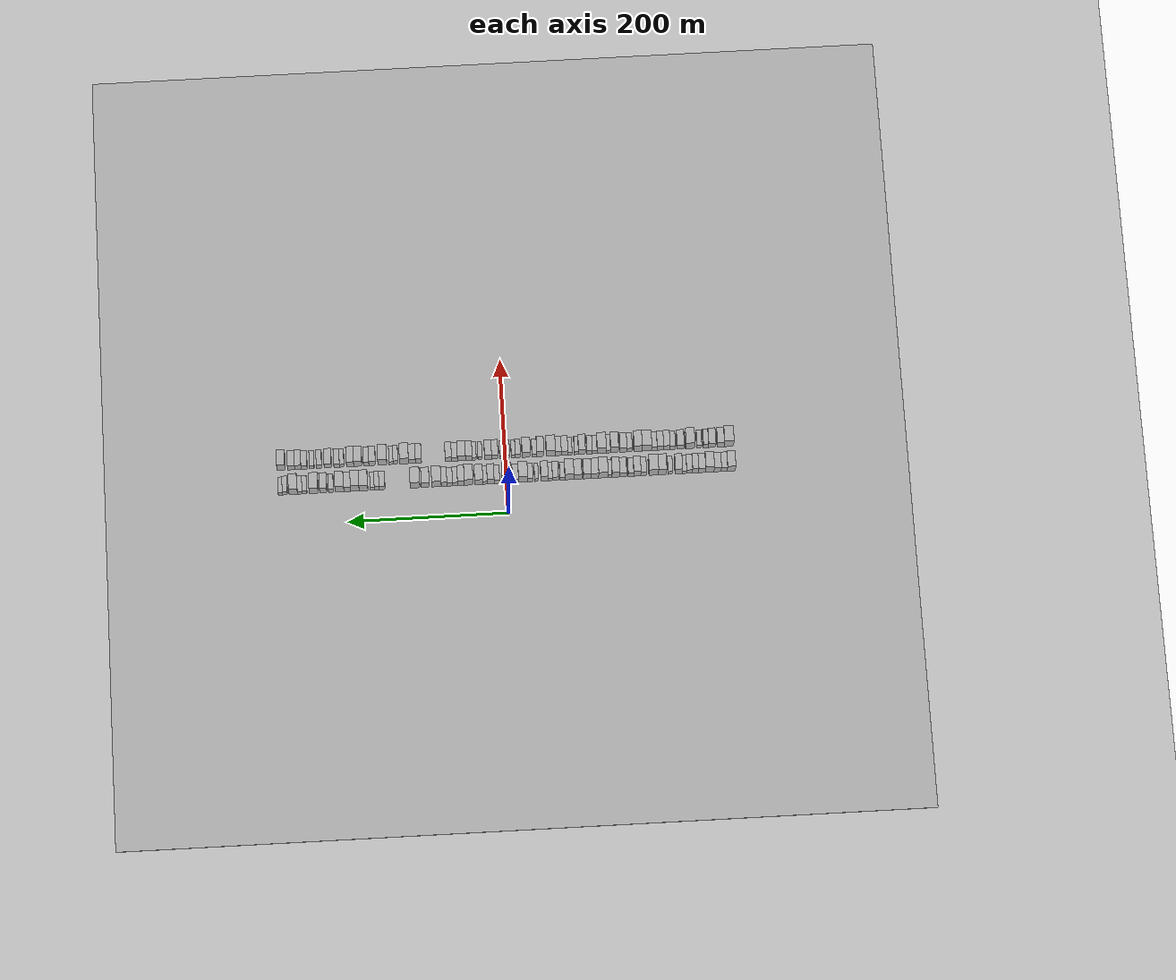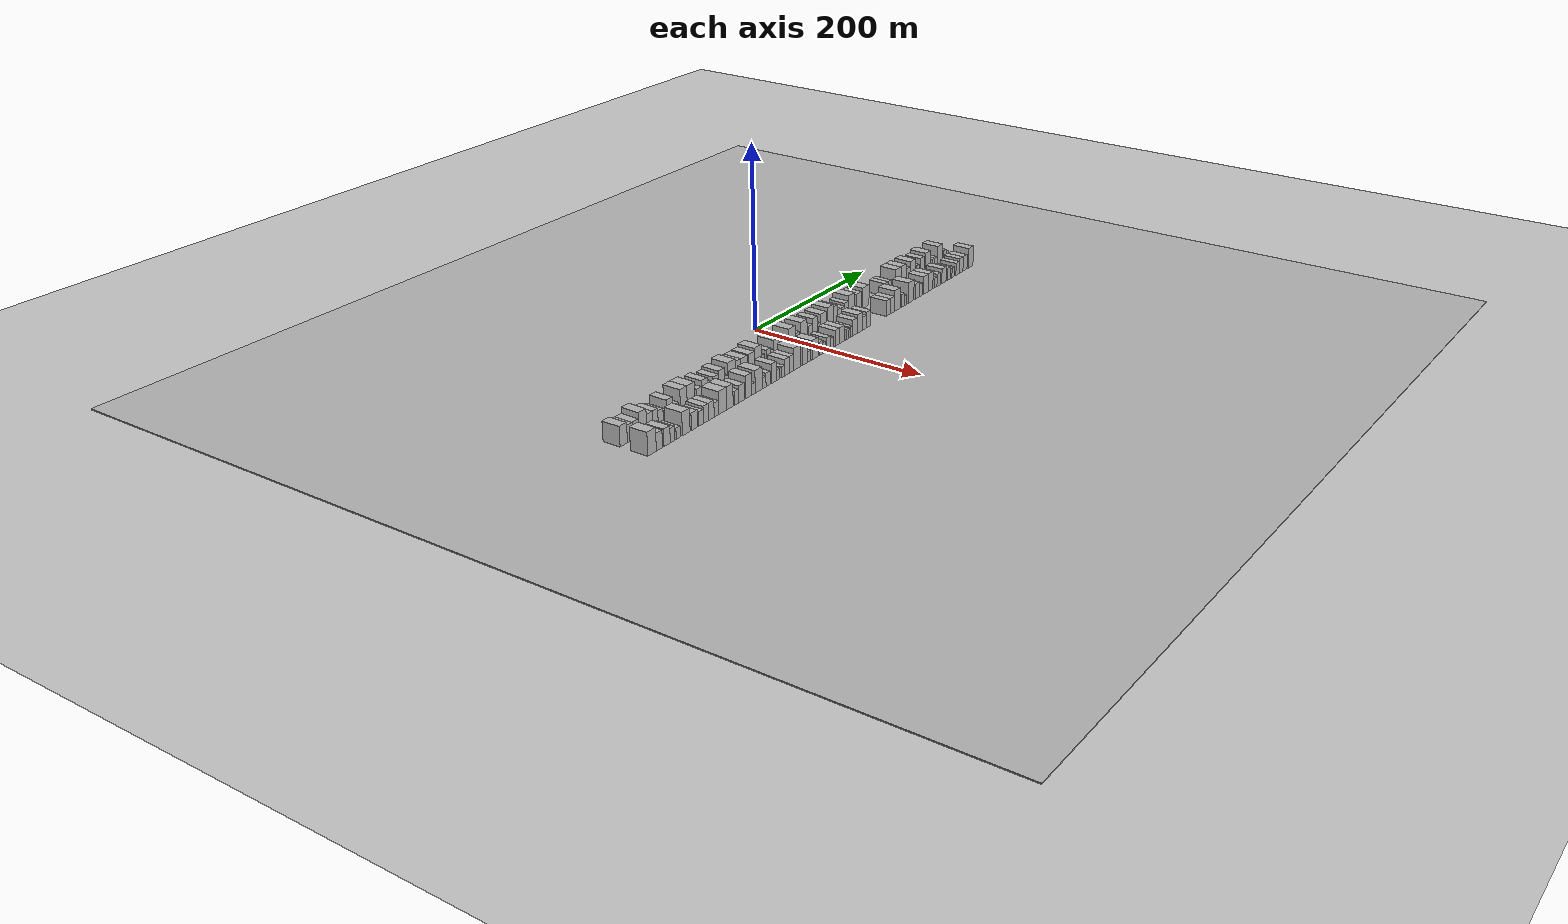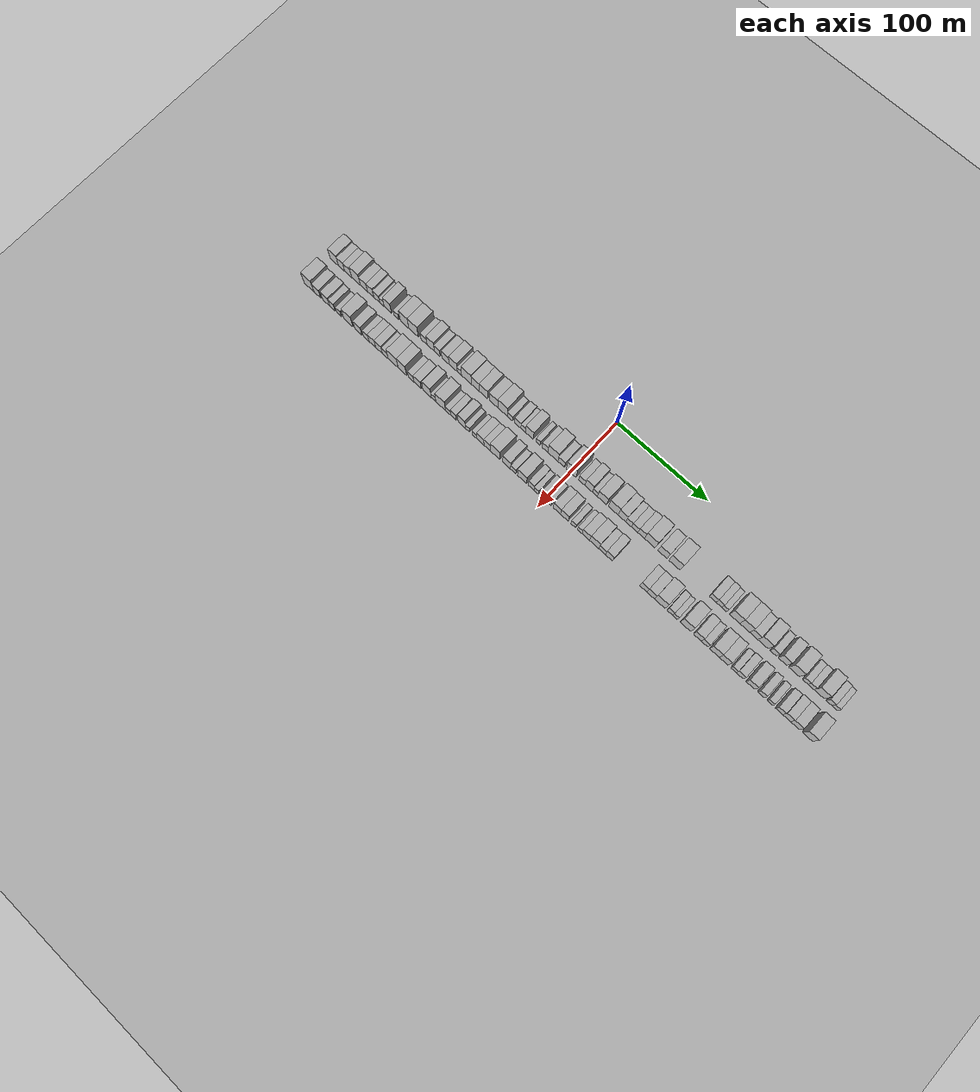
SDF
<?xml version="1.0" encoding="utf-8"?>

<sdf version="1.6">

   <world name="default">

      <gui fullscreen="0">

         <camera name="user_camera">

            <pose>-15 0 4.57585 0 0 0</pose>

            <view_controller>orbit</view_controller>

         </camera>

      </gui>

      <scene>

         <sky>

           <clouds>

             <speed>12</speed>

           </clouds>

         </sky>

         <ambient>0.4 0.4 0.4 1</ambient>

         <background>0.7 0.7 0.7 1</background>

         <shadows>1</shadows>

      </scene>

      <gravity>0 0 -9.8066</gravity>

      <magnetic_field>6e-06 2.3e-05 -4.2e-05</magnetic_field>

      <physics default="0" name="default_physics" type="ode">

         <ode>

            <solver>

               <type>quick</type>

               <iters>10</iters>

               <sor>1.0</sor>

               <use_dynamic_moi_rescaling>0</use_dynamic_moi_rescaling>

            </solver>

            <constraints>

               <cfm>0</cfm>

               <erp>0.2</erp>

               <contact_max_correcting_vel>100</contact_max_correcting_vel>

               <contact_surface_layer>0.001</contact_surface_layer>

            </constraints>

         </ode>

         <max_step_size>0.004</max_step_size>

         <real_time_factor>1</real_time_factor>

         <real_time_update_rate>250</real_time_update_rate>

      </physics>

      <light name="sun" type="directional">

         <cast_shadows>1</cast_shadows>

         <pose>0 0 10 0 0 0</pose>

         <diffuse>0.8 0.8 0.8 1</diffuse>

         <specular>0.2 0.2 0.2 1</specular>

         <attenuation>

            <range>1000</range>

            <constant>0.9</constant>

            <linear>0.01</linear>

            <quadratic>0.001</quadratic>

         </attenuation>

         <direction>-0.5 0.1 -0.9</direction>

      </light>

      <include>

         <name>ground_plane_1</name>

         <uri>model://HANNAS_ground_plane</uri>

         <pose>0 0 0  0 0 0</pose>

      </include>

      <include>

         <name>ground_plane_2</name>

         <uri>model://HANNAS_ground_plane</uri>

         <pose>100 0 0  0 0 0</pose>

      </include>

      <model name="building_1">

         <static>1</static>

         <pose frame="">50.0000 -278.9319 0 0.000000 0.000000 0.000000</pose>

         <link name="link">

            <pose frame="">0 0 10.50 0 0 0</pose>

            <collision name="collision">

               <geometry>

                  <box>

                     <size>20.0000 10.1363 21.0000</size>

                  </box>

               </geometry>

               <max_contacts>10</max_contacts>

               <surface>

                  <contact>

                     <ode/>

                  </contact>

                  <bounce/>

                  <friction>

                     <torsional>

                        <ode/>

                     </torsional>

                     <ode/>

                  </friction>

               </surface>

            </collision>

            <visual name="visual">

               <cast_shadows>0</cast_shadows>

               <geometry>

                  <box>

                     <size>20.0000 10.1363 21.0000</size>

                  </box>

               </geometry>

               <material>

                  <script>

                     <uri>model://HANNAS_wall/materials/scripts</uri>

                     <uri>model://HANNAS_wall/materials/textures</uri>

                     <name>vrc/HANNAS_wall</name>

                  </script>

               </material>

            </visual>

            <self_collide>0</self_collide>

            <enable_wind>0</enable_wind>

            <kinematic>0</kinematic>

         </link>

      </model>

      <model name="building_2">

         <static>1</static>

         <pose frame="">50.0000 -270.0899 0 0.000000 0.000000 0.000000</pose>

         <link name="link">

            <pose frame="">0 0 9.00 0 0 0</pose>

            <collision name="collision">

               <geometry>

                  <box>

                     <size>20.0000 7.5476 18.0000</size>

                  </box>

               </geometry>

               <max_contacts>10</max_contacts>

               <surface>

                  <contact>

                     <ode/>

                  </contact>

                  <bounce/>

                  <friction>

                     <torsional>

                        <ode/>

                     </torsional>

                     <ode/>

                  </friction>

               </surface>

            </collision>

            <visual name="visual">

               <cast_shadows>0</cast_shadows>

               <geometry>

                  <box>

                     <size>20.0000 7.5476 18.0000</size>

                  </box>

               </geometry>

               <material>

                  <script>

                     <uri>model://HANNAS_wall/materials/scripts</uri>

                     <uri>model://HANNAS_wall/materials/textures</uri>

                     <name>vrc/HANNAS_wall</name>

                  </script>

               </material>

            </visual>

            <self_collide>0</self_collide>

            <enable_wind>0</enable_wind>

            <kinematic>0</kinematic>

         </link>

      </model>

      <model name="building_3">

         <static>1</static>

         <pose frame="">50.0000 -261.8540 0 0.000000 0.000000 0.000000</pose>

         <link name="link">

            <pose frame="">0 0 9.00 0 0 0</pose>

            <collision name="collision">

               <geometry>

                  <box>

                     <size>20.0000 8.9242 18.0000</size>

                  </box>

               </geometry>

               <max_contacts>10</max_contacts>

               <surface>

                  <contact>

                     <ode/>

                  </contact>

                  <bounce/>

                  <friction>

                     <torsional>

                        <ode/>

                     </torsional>

                     <ode/>

                  </friction>

               </surface>

            </collision>

            <visual name="visual">

               <cast_shadows>0</cast_shadows>

               <geometry>

                  <box>

                     <size>20.0000 8.9242 18.0000</size>

                  </box>

               </geometry>

               <material>

                  <script>

                     <uri>model://HANNAS_wall/materials/scripts</uri>

                     <uri>model://HANNAS_wall/materials/textures</uri>

                     <name>vrc/HANNAS_wall</name>

                  </script>

               </material>

            </visual>

            <self_collide>0</self_collide>

            <enable_wind>0</enable_wind>

            <kinematic>0</kinematic>

         </link>

      </model>

      <model name="building_4">

         <static>1</static>

         <pose frame="">50.0000 -252.0789 0 0.000000 0.000000 0.000000</pose>

         <link name="link">

            <pose frame="">0 0 12.00 0 0 0</pose>

            <collision name="collision">

               <geometry>

                  <box>

                     <size>20.0000 10.6259 24.0000</size>

                  </box>

               </geometry>

               <max_contacts>10</max_contacts>

               <surface>

                  <contact>

                     <ode/>

                  </contact>

                  <bounce/>

                  <friction>

                     <torsional>

                        <ode/>

                     </torsional>

                     <ode/>

                  </friction>

               </surface>

            </collision>

            <visual name="visual">

               <cast_shadows>0</cast_shadows>

               <geometry>

                  <box>

                     <size>20.0000 10.6259 24.0000</size>

                  </box>

               </geometry>

               <material>

                  <script>

                     <uri>model://HANNAS_wall/materials/scripts</uri>

                     <uri>model://HANNAS_wall/materials/textures</uri>

                     <name>vrc/HANNAS_wall</name>

                  </script>

               </material>

            </visual>

            <self_collide>0</self_collide>

            <enable_wind>0</enable_wind>

            <kinematic>0</kinematic>

         </link>

      </model>

      <model name="building_5">

         <static>1</static>

         <pose frame="">50.0000 -242.4415 0 0.000000 0.000000 0.000000</pose>

         <link name="link">

            <pose frame="">0 0 9.00 0 0 0</pose>

            <collision name="collision">

               <geometry>

                  <box>

                     <size>20.0000 8.6490 18.0000</size>

                  </box>

               </geometry>

               <max_contacts>10</max_contacts>

               <surface>

                  <contact>

                     <ode/>

                  </contact>

                  <bounce/>

                  <friction>

                     <torsional>

                        <ode/>

                     </torsional>

                     <ode/>

                  </friction>

               </surface>

            </collision>

            <visual name="visual">

               <cast_shadows>0</cast_shadows>

               <geometry>

                  <box>

                     <size>20.0000 8.6490 18.0000</size>

                  </box>

               </geometry>

               <material>

                  <script>

                     <uri>model://HANNAS_wall/materials/scripts</uri>

                     <uri>model://HANNAS_wall/materials/textures</uri>

                     <name>vrc/HANNAS_wall</name>

                  </script>

               </material>

            </visual>

            <self_collide>0</self_collide>

            <enable_wind>0</enable_wind>

            <kinematic>0</kinematic>

         </link>

      </model>

      <model name="building_6">

         <static>1</static>

         <pose frame="">50.0000 -234.3354 0 0.000000 0.000000 0.000000</pose>

         <link name="link">

            <pose frame="">0 0 9.00 0 0 0</pose>

            <collision name="collision">

               <geometry>

                  <box>

                     <size>20.0000 7.5632 18.0000</size>

                  </box>

               </geometry>

               <max_contacts>10</max_contacts>

               <surface>

                  <contact>

                     <ode/>

                  </contact>

                  <bounce/>

                  <friction>

                     <torsional>

                        <ode/>

                     </torsional>

                     <ode/>

                  </friction>

               </surface>

            </collision>

            <visual name="visual">

               <cast_shadows>0</cast_shadows>

               <geometry>

                  <box>

                     <size>20.0000 7.5632 18.0000</size>

                  </box>

               </geometry>

               <material>

                  <script>

                     <uri>model://HANNAS_wall/materials/scripts</uri>

                     <uri>model://HANNAS_wall/materials/textures</uri>

                     <name>vrc/HANNAS_wall</name>

                  </script>

               </material>

            </visual>

            <self_collide>0</self_collide>

            <enable_wind>0</enable_wind>

            <kinematic>0</kinematic>

         </link>

      </model>

      <model name="building_7">

         <static>1</static>

         <pose frame="">50.0000 -226.8695 0 0.000000 0.000000 0.000000</pose>

         <link name="link">

            <pose frame="">0 0 7.50 0 0 0</pose>

            <collision name="collision">

               <geometry>

                  <box>

                     <size>20.0000 7.3687 15.0000</size>

                  </box>

               </geometry>

               <max_contacts>10</max_contacts>

               <surface>

                  <contact>

                     <ode/>

                  </contact>

                  <bounce/>

                  <friction>

                     <torsional>

                        <ode/>

                     </torsional>

                     <ode/>

                  </friction>

               </surface>

            </collision>

            <visual name="visual">

               <cast_shadows>0</cast_shadows>

               <geometry>

                  <box>

                     <size>20.0000 7.3687 15.0000</size>

                  </box>

               </geometry>

               <material>

                  <script>

                     <uri>model://HANNAS_wall/materials/scripts</uri>

                     <uri>model://HANNAS_wall/materials/textures</uri>

                     <name>vrc/HANNAS_wall</name>

                  </script>

               </material>

            </visual>

            <self_collide>0</self_collide>

            <enable_wind>0</enable_wind>

            <kinematic>0</kinematic>

         </link>

      </model>

      <model name="building_8">

         <static>1</static>

         <pose frame="">50.0000 -220.5468 0 0.000000 0.000000 0.000000</pose>

         <link name="link">

            <pose frame="">0 0 6.00 0 0 0</pose>

            <collision name="collision">

               <geometry>

                  <box>

                     <size>20.0000 5.2767 12.0000</size>

                  </box>

               </geometry>

               <max_contacts>10</max_contacts>

               <surface>

                  <contact>

                     <ode/>

                  </contact>

                  <bounce/>

                  <friction>

                     <torsional>

                        <ode/>

                     </torsional>

                     <ode/>

                  </friction>

               </surface>

            </collision>

            <visual name="visual">

               <cast_shadows>0</cast_shadows>

               <geometry>

                  <box>

                     <size>20.0000 5.2767 12.0000</size>

                  </box>

               </geometry>

               <material>

                  <script>

                     <uri>model://HANNAS_wall/materials/scripts</uri>

                     <uri>model://HANNAS_wall/materials/textures</uri>

                     <name>vrc/HANNAS_wall</name>

                  </script>

               </material>

            </visual>

            <self_collide>0</self_collide>

            <enable_wind>0</enable_wind>

            <kinematic>0</kinematic>

         </link>

      </model>

      <model name="building_9">

         <static>1</static>

         <pose frame="">50.0000 -213.4401 0 0.000000 0.000000 0.000000</pose>

         <link name="link">

            <pose frame="">0 0 10.50 0 0 0</pose>

            <collision name="collision">

               <geometry>

                  <box>

                     <size>20.0000 8.9366 21.0000</size>

                  </box>

               </geometry>

               <max_contacts>10</max_contacts>

               <surface>

                  <contact>

                     <ode/>

                  </contact>

                  <bounce/>

                  <friction>

                     <torsional>

                        <ode/>

                     </torsional>

                     <ode/>

                  </friction>

               </surface>

            </collision>

            <visual name="visual">

               <cast_shadows>0</cast_shadows>

               <geometry>

                  <box>

                     <size>20.0000 8.9366 21.0000</size>

                  </box>

               </geometry>

               <material>

                  <script>

                     <uri>model://HANNAS_wall/materials/scripts</uri>

                     <uri>model://HANNAS_wall/materials/textures</uri>

                     <name>vrc/HANNAS_wall</name>

                  </script>

               </material>

            </visual>

            <self_collide>0</self_collide>

            <enable_wind>0</enable_wind>

            <kinematic>0</kinematic>

         </link>

      </model>

      <model name="building_10">

         <static>1</static>

         <pose frame="">50.0000 -203.0445 0 0.000000 0.000000 0.000000</pose>

         <link name="link">

            <pose frame="">0 0 6.00 0 0 0</pose>

            <collision name="collision">

               <geometry>

                  <box>

                     <size>20.0000 5.8547 12.0000</size>

                  </box>

               </geometry>

               <max_contacts>10</max_contacts>

               <surface>

                  <contact>

                     <ode/>

                  </contact>

                  <bounce/>

                  <friction>

                     <torsional>

                        <ode/>

                     </torsional>

                     <ode/>

                  </friction>

               </surface>

            </collision>

            <visual name="visual">

               <cast_shadows>0</cast_shadows>

               <geometry>

                  <box>

                     <size>20.0000 5.8547 12.0000</size>

                  </box>

               </geometry>

               <material>

                  <script>

                     <uri>model://HANNAS_wall/materials/scripts</uri>

                     <uri>model://HANNAS_wall/materials/textures</uri>

                     <name>vrc/HANNAS_wall</name>

                  </script>

               </material>

            </visual>

            <self_collide>0</self_collide>

            <enable_wind>0</enable_wind>

            <kinematic>0</kinematic>

         </link>

      </model>

      <model name="building_11">

         <static>1</static>

         <pose frame="">50.0000 -193.0711 0 0.000000 0.000000 0.000000</pose>

         <link name="link">

            <pose frame="">0 0 12.00 0 0 0</pose>

            <collision name="collision">

               <geometry>

                  <box>

                     <size>20.0000 10.0920 24.0000</size>

                  </box>

               </geometry>

               <max_contacts>10</max_contacts>

               <surface>

                  <contact>

                     <ode/>

                  </contact>

                  <bounce/>

                  <friction>

                     <torsional>

                        <ode/>

                     </torsional>

                     <ode/>

                  </friction>

               </surface>

            </collision>

            <visual name="visual">

               <cast_shadows>0</cast_shadows>

               <geometry>

                  <box>

                     <size>20.0000 10.0920 24.0000</size>

                  </box>

               </geometry>

               <material>

                  <script>

                     <uri>model://HANNAS_wall/materials/scripts</uri>

                     <uri>model://HANNAS_wall/materials/textures</uri>

                     <name>vrc/HANNAS_wall</name>

                  </script>

               </material>

            </visual>

            <self_collide>0</self_collide>

            <enable_wind>0</enable_wind>

            <kinematic>0</kinematic>

         </link>

      </model>

      <model name="building_12">

         <static>1</static>

         <pose frame="">50.0000 -182.2278 0 0.000000 0.000000 0.000000</pose>

         <link name="link">

            <pose frame="">0 0 12.00 0 0 0</pose>

            <collision name="collision">

               <geometry>

                  <box>

                     <size>20.0000 11.5945 24.0000</size>

                  </box>

               </geometry>

               <max_contacts>10</max_contacts>

               <surface>

                  <contact>

                     <ode/>

                  </contact>

                  <bounce/>

                  <friction>

                     <torsional>

                        <ode/>

                     </torsional>

                     <ode/>

                  </friction>

               </surface>

            </collision>

            <visual name="visual">

               <cast_shadows>0</cast_shadows>

               <geometry>

                  <box>

                     <size>20.0000 11.5945 24.0000</size>

                  </box>

               </geometry>

               <material>

                  <script>

                     <uri>model://HANNAS_wall/materials/scripts</uri>

                     <uri>model://HANNAS_wall/materials/textures</uri>

                     <name>vrc/HANNAS_wall</name>

                  </script>

               </material>

            </visual>

            <self_collide>0</self_collide>

            <enable_wind>0</enable_wind>

            <kinematic>0</kinematic>

         </link>

      </model>

      <model name="building_13">

         <static>1</static>

         <pose frame="">50.0000 -169.8044 0 0.000000 0.000000 0.000000</pose>

         <link name="link">

            <pose frame="">0 0 7.50 0 0 0</pose>

            <collision name="collision">

               <geometry>

                  <box>

                     <size>20.0000 7.2523 15.0000</size>

                  </box>

               </geometry>

               <max_contacts>10</max_contacts>

               <surface>

                  <contact>

                     <ode/>

                  </contact>

                  <bounce/>

                  <friction>

                     <torsional>

                        <ode/>

                     </torsional>

                     <ode/>

                  </friction>

               </surface>

            </collision>

            <visual name="visual">

               <cast_shadows>0</cast_shadows>

               <geometry>

                  <box>

                     <size>20.0000 7.2523 15.0000</size>

                  </box>

               </geometry>

               <material>

                  <script>

                     <uri>model://HANNAS_wall/materials/scripts</uri>

                     <uri>model://HANNAS_wall/materials/textures</uri>

                     <name>vrc/HANNAS_wall</name>

                  </script>

               </material>

            </visual>

            <self_collide>0</self_collide>

            <enable_wind>0</enable_wind>

            <kinematic>0</kinematic>

         </link>

      </model>

      <model name="building_14">

         <static>1</static>

         <pose frame="">50.0000 -161.7620 0 0.000000 0.000000 0.000000</pose>

         <link name="link">

            <pose frame="">0 0 10.50 0 0 0</pose>

            <collision name="collision">

               <geometry>

                  <box>

                     <size>20.0000 8.8325 21.0000</size>

                  </box>

               </geometry>

               <max_contacts>10</max_contacts>

               <surface>

                  <contact>

                     <ode/>

                  </contact>

                  <bounce/>

                  <friction>

                     <torsional>

                        <ode/>

                     </torsional>

                     <ode/>

                  </friction>

               </surface>

            </collision>

            <visual name="visual">

               <cast_shadows>0</cast_shadows>

               <geometry>

                  <box>

                     <size>20.0000 8.8325 21.0000</size>

                  </box>

               </geometry>

               <material>

                  <script>

                     <uri>model://HANNAS_wall/materials/scripts</uri>

                     <uri>model://HANNAS_wall/materials/textures</uri>

                     <name>vrc/HANNAS_wall</name>

                  </script>

               </material>

            </visual>

            <self_collide>0</self_collide>

            <enable_wind>0</enable_wind>

            <kinematic>0</kinematic>

         </link>

      </model>

      <model name="building_15">

         <static>1</static>

         <pose frame="">50.0000 -153.9001 0 0.000000 0.000000 0.000000</pose>

         <link name="link">

            <pose frame="">0 0 7.50 0 0 0</pose>

            <collision name="collision">

               <geometry>

                  <box>

                     <size>20.0000 6.8913 15.0000</size>

                  </box>

               </geometry>

               <max_contacts>10</max_contacts>

               <surface>

                  <contact>

                     <ode/>

                  </contact>

                  <bounce/>

                  <friction>

                     <torsional>

                        <ode/>

                     </torsional>

                     <ode/>

                  </friction>

               </surface>

            </collision>

            <visual name="visual">

               <cast_shadows>0</cast_shadows>

               <geometry>

                  <box>

                     <size>20.0000 6.8913 15.0000</size>

                  </box>

               </geometry>

               <material>

                  <script>

                     <uri>model://HANNAS_wall/materials/scripts</uri>

                     <uri>model://HANNAS_wall/materials/textures</uri>

                     <name>vrc/HANNAS_wall</name>

                  </script>

               </material>

            </visual>

            <self_collide>0</self_collide>

            <enable_wind>0</enable_wind>

            <kinematic>0</kinematic>

         </link>

      </model>

      <model name="building_16">

         <static>1</static>

         <pose frame="">50.0000 -144.1862 0 0.000000 0.000000 0.000000</pose>

         <link name="link">

            <pose frame="">0 0 9.00 0 0 0</pose>

            <collision name="collision">

               <geometry>

                  <box>

                     <size>20.0000 8.5365 18.0000</size>

                  </box>

               </geometry>

               <max_contacts>10</max_contacts>

               <surface>

                  <contact>

                     <ode/>

                  </contact>

                  <bounce/>

                  <friction>

                     <torsional>

                        <ode/>

                     </torsional>

                     <ode/>

                  </friction>

               </surface>

            </collision>

            <visual name="visual">

               <cast_shadows>0</cast_shadows>

               <geometry>

                  <box>

                     <size>20.0000 8.5365 18.0000</size>

                  </box>

               </geometry>

               <material>

                  <script>

                     <uri>model://HANNAS_wall/materials/scripts</uri>

                     <uri>model://HANNAS_wall/materials/textures</uri>

                     <name>vrc/HANNAS_wall</name>

                  </script>

               </material>

            </visual>

            <self_collide>0</self_collide>

            <enable_wind>0</enable_wind>

            <kinematic>0</kinematic>

         </link>

      </model>

      <model name="building_17">

         <static>1</static>

         <pose frame="">50.0000 -135.1311 0 0.000000 0.000000 0.000000</pose>

         <link name="link">

            <pose frame="">0 0 10.50 0 0 0</pose>

            <collision name="collision">

               <geometry>

                  <box>

                     <size>20.0000 9.5737 21.0000</size>

                  </box>

               </geometry>

               <max_contacts>10</max_contacts>

               <surface>

                  <contact>

                     <ode/>

                  </contact>

                  <bounce/>

                  <friction>

                     <torsional>

                        <ode/>

                     </torsional>

                     <ode/>

                  </friction>

               </surface>

            </collision>

            <visual name="visual">

               <cast_shadows>0</cast_shadows>

               <geometry>

                  <box>

                     <size>20.0000 9.5737 21.0000</size>

                  </box>

               </geometry>

               <material>

                  <script>

                     <uri>model://HANNAS_wall/materials/scripts</uri>

                     <uri>model://HANNAS_wall/materials/textures</uri>

                     <name>vrc/HANNAS_wall</name>

                  </script>

               </material>

            </visual>

            <self_collide>0</self_collide>

            <enable_wind>0</enable_wind>

            <kinematic>0</kinematic>

         </link>

      </model>

      <model name="building_18">

         <static>1</static>

         <pose frame="">50.0000 -127.8326 0 0.000000 0.000000 0.000000</pose>

         <link name="link">

            <pose frame="">0 0 6.00 0 0 0</pose>

            <collision name="collision">

               <geometry>

                  <box>

                     <size>20.0000 5.0233 12.0000</size>

                  </box>

               </geometry>

               <max_contacts>10</max_contacts>

               <surface>

                  <contact>

                     <ode/>

                  </contact>

                  <bounce/>

                  <friction>

                     <torsional>

                        <ode/>

                     </torsional>

                     <ode/>

                  </friction>

               </surface>

            </collision>

            <visual name="visual">

               <cast_shadows>0</cast_shadows>

               <geometry>

                  <box>

                     <size>20.0000 5.0233 12.0000</size>

                  </box>

               </geometry>

               <material>

                  <script>

                     <uri>model://HANNAS_wall/materials/scripts</uri>

                     <uri>model://HANNAS_wall/materials/textures</uri>

                     <name>vrc/HANNAS_wall</name>

                  </script>

               </material>

            </visual>

            <self_collide>0</self_collide>

            <enable_wind>0</enable_wind>

            <kinematic>0</kinematic>

         </link>

      </model>

      <model name="building_19">

         <static>1</static>

         <pose frame="">50.0000 -119.4954 0 0.000000 0.000000 0.000000</pose>

         <link name="link">

            <pose frame="">0 0 12.00 0 0 0</pose>

            <collision name="collision">

               <geometry>

                  <box>

                     <size>20.0000 11.6512 24.0000</size>

                  </box>

               </geometry>

               <max_contacts>10</max_contacts>

               <surface>

                  <contact>

                     <ode/>

                  </contact>

                  <bounce/>

                  <friction>

                     <torsional>

                        <ode/>

                     </torsional>

                     <ode/>

                  </friction>

               </surface>

            </collision>

            <visual name="visual">

               <cast_shadows>0</cast_shadows>

               <geometry>

                  <box>

                     <size>20.0000 11.6512 24.0000</size>

                  </box>

               </geometry>

               <material>

                  <script>

                     <uri>model://HANNAS_wall/materials/scripts</uri>

                     <uri>model://HANNAS_wall/materials/textures</uri>

                     <name>vrc/HANNAS_wall</name>

                  </script>

               </material>

            </visual>

            <self_collide>0</self_collide>

            <enable_wind>0</enable_wind>

            <kinematic>0</kinematic>

         </link>

      </model>

      <model name="building_20">

         <static>1</static>

         <pose frame="">50.0000 -109.1221 0 0.000000 0.000000 0.000000</pose>

         <link name="link">

            <pose frame="">0 0 10.50 0 0 0</pose>

            <collision name="collision">

               <geometry>

                  <box>

                     <size>20.0000 9.0954 21.0000</size>

                  </box>

               </geometry>

               <max_contacts>10</max_contacts>

               <surface>

                  <contact>

                     <ode/>

                  </contact>

                  <bounce/>

                  <friction>

                     <torsional>

                        <ode/>

                     </torsional>

                     <ode/>

                  </friction>

               </surface>

            </collision>

            <visual name="visual">

               <cast_shadows>0</cast_shadows>

               <geometry>

                  <box>

                     <size>20.0000 9.0954 21.0000</size>

                  </box>

               </geometry>

               <material>

                  <script>

                     <uri>model://HANNAS_wall/materials/scripts</uri>

                     <uri>model://HANNAS_wall/materials/textures</uri>

                     <name>vrc/HANNAS_wall</name>

                  </script>

               </material>

            </visual>

            <self_collide>0</self_collide>

            <enable_wind>0</enable_wind>

            <kinematic>0</kinematic>

         </link>

      </model>

      <model name="building_21">

         <static>1</static>

         <pose frame="">50.0000 -99.6407 0 0.000000 0.000000 0.000000</pose>

         <link name="link">

            <pose frame="">0 0 10.50 0 0 0</pose>

            <collision name="collision">

               <geometry>

                  <box>

                     <size>20.0000 9.8675 21.0000</size>

                  </box>

               </geometry>

               <max_contacts>10</max_contacts>

               <surface>

                  <contact>

                     <ode/>

                  </contact>

                  <bounce/>

                  <friction>

                     <torsional>

                        <ode/>

                     </torsional>

                     <ode/>

                  </friction>

               </surface>

            </collision>

            <visual name="visual">

               <cast_shadows>0</cast_shadows>

               <geometry>

                  <box>

                     <size>20.0000 9.8675 21.0000</size>

                  </box>

               </geometry>

               <material>

                  <script>

                     <uri>model://HANNAS_wall/materials/scripts</uri>

                     <uri>model://HANNAS_wall/materials/textures</uri>

                     <name>vrc/HANNAS_wall</name>

                  </script>

               </material>

            </visual>

            <self_collide>0</self_collide>

            <enable_wind>0</enable_wind>

            <kinematic>0</kinematic>

         </link>

      </model>

      <model name="building_22">

         <static>1</static>

         <pose frame="">50.0000 -87.7980 0 0.000000 0.000000 0.000000</pose>

         <link name="link">

            <pose frame="">0 0 10.50 0 0 0</pose>

            <collision name="collision">

               <geometry>

                  <box>

                     <size>20.0000 9.8178 21.0000</size>

                  </box>

               </geometry>

               <max_contacts>10</max_contacts>

               <surface>

                  <contact>

                     <ode/>

                  </contact>

                  <bounce/>

                  <friction>

                     <torsional>

                        <ode/>

                     </torsional>

                     <ode/>

                  </friction>

               </surface>

            </collision>

            <visual name="visual">

               <cast_shadows>0</cast_shadows>

               <geometry>

                  <box>

                     <size>20.0000 9.8178 21.0000</size>

                  </box>

               </geometry>

               <material>

                  <script>

                     <uri>model://HANNAS_wall/materials/scripts</uri>

                     <uri>model://HANNAS_wall/materials/textures</uri>

                     <name>vrc/HANNAS_wall</name>

                  </script>

               </material>

            </visual>

            <self_collide>0</self_collide>

            <enable_wind>0</enable_wind>

            <kinematic>0</kinematic>

         </link>

      </model>

      <model name="building_23">

         <static>1</static>

         <pose frame="">50.0000 -77.2852 0 0.000000 0.000000 0.000000</pose>

         <link name="link">

            <pose frame="">0 0 12.00 0 0 0</pose>

            <collision name="collision">

               <geometry>

                  <box>

                     <size>20.0000 11.2078 24.0000</size>

                  </box>

               </geometry>

               <max_contacts>10</max_contacts>

               <surface>

                  <contact>

                     <ode/>

                  </contact>

                  <bounce/>

                  <friction>

                     <torsional>

                        <ode/>

                     </torsional>

                     <ode/>

                  </friction>

               </surface>

            </collision>

            <visual name="visual">

               <cast_shadows>0</cast_shadows>

               <geometry>

                  <box>

                     <size>20.0000 11.2078 24.0000</size>

                  </box>

               </geometry>

               <material>

                  <script>

                     <uri>model://HANNAS_wall/materials/scripts</uri>

                     <uri>model://HANNAS_wall/materials/textures</uri>

                     <name>vrc/HANNAS_wall</name>

                  </script>

               </material>

            </visual>

            <self_collide>0</self_collide>

            <enable_wind>0</enable_wind>

            <kinematic>0</kinematic>

         </link>

      </model>

      <model name="building_24">

         <static>1</static>

         <pose frame="">50.0000 -68.6890 0 0.000000 0.000000 0.000000</pose>

         <link name="link">

            <pose frame="">0 0 6.00 0 0 0</pose>

            <collision name="collision">

               <geometry>

                  <box>

                     <size>20.0000 5.9847 12.0000</size>

                  </box>

               </geometry>

               <max_contacts>10</max_contacts>

               <surface>

                  <contact>

                     <ode/>

                  </contact>

                  <bounce/>

                  <friction>

                     <torsional>

                        <ode/>

                     </torsional>

                     <ode/>

                  </friction>

               </surface>

            </collision>

            <visual name="visual">

               <cast_shadows>0</cast_shadows>

               <geometry>

                  <box>

                     <size>20.0000 5.9847 12.0000</size>

                  </box>

               </geometry>

               <material>

                  <script>

                     <uri>model://HANNAS_wall/materials/scripts</uri>

                     <uri>model://HANNAS_wall/materials/textures</uri>

                     <name>vrc/HANNAS_wall</name>

                  </script>

               </material>

            </visual>

            <self_collide>0</self_collide>

            <enable_wind>0</enable_wind>

            <kinematic>0</kinematic>

         </link>

      </model>

      <model name="building_25">

         <static>1</static>

         <pose frame="">50.0000 -59.9812 0 0.000000 0.000000 0.000000</pose>

         <link name="link">

            <pose frame="">0 0 7.50 0 0 0</pose>

            <collision name="collision">

               <geometry>

                  <box>

                     <size>20.0000 7.4309 15.0000</size>

                  </box>

               </geometry>

               <max_contacts>10</max_contacts>

               <surface>

                  <contact>

                     <ode/>

                  </contact>

                  <bounce/>

                  <friction>

                     <torsional>

                        <ode/>

                     </torsional>

                     <ode/>

                  </friction>

               </surface>

            </collision>

            <visual name="visual">

               <cast_shadows>0</cast_shadows>

               <geometry>

                  <box>

                     <size>20.0000 7.4309 15.0000</size>

                  </box>

               </geometry>

               <material>

                  <script>

                     <uri>model://HANNAS_wall/materials/scripts</uri>

                     <uri>model://HANNAS_wall/materials/textures</uri>

                     <name>vrc/HANNAS_wall</name>

                  </script>

               </material>

            </visual>

            <self_collide>0</self_collide>

            <enable_wind>0</enable_wind>

            <kinematic>0</kinematic>

         </link>

      </model>

      <model name="building_26">

         <static>1</static>

         <pose frame="">50.0000 -53.5605 0 0.000000 0.000000 0.000000</pose>

         <link name="link">

            <pose frame="">0 0 6.00 0 0 0</pose>

            <collision name="collision">

               <geometry>

                  <box>

                     <size>20.0000 5.4105 12.0000</size>

                  </box>

               </geometry>

               <max_contacts>10</max_contacts>

               <surface>

                  <contact>

                     <ode/>

                  </contact>

                  <bounce/>

                  <friction>

                     <torsional>

                        <ode/>

                     </torsional>

                     <ode/>

                  </friction>

               </surface>

            </collision>

            <visual name="visual">

               <cast_shadows>0</cast_shadows>

               <geometry>

                  <box>

                     <size>20.0000 5.4105 12.0000</size>

                  </box>

               </geometry>

               <material>

                  <script>

                     <uri>model://HANNAS_wall/materials/scripts</uri>

                     <uri>model://HANNAS_wall/materials/textures</uri>

                     <name>vrc/HANNAS_wall</name>

                  </script>

               </material>

            </visual>

            <self_collide>0</self_collide>

            <enable_wind>0</enable_wind>

            <kinematic>0</kinematic>

         </link>

      </model>

      <model name="building_27">

         <static>1</static>

         <pose frame="">50.0000 -46.4148 0 0.000000 0.000000 0.000000</pose>

         <link name="link">

            <pose frame="">0 0 10.50 0 0 0</pose>

            <collision name="collision">

               <geometry>

                  <box>

                     <size>20.0000 8.8810 21.0000</size>

                  </box>

               </geometry>

               <max_contacts>10</max_contacts>

               <surface>

                  <contact>

                     <ode/>

                  </contact>

                  <bounce/>

                  <friction>

                     <torsional>

                        <ode/>

                     </torsional>

                     <ode/>

                  </friction>

               </surface>

            </collision>

            <visual name="visual">

               <cast_shadows>0</cast_shadows>

               <geometry>

                  <box>

                     <size>20.0000 8.8810 21.0000</size>

                  </box>

               </geometry>

               <material>

                  <script>

                     <uri>model://HANNAS_wall/materials/scripts</uri>

                     <uri>model://HANNAS_wall/materials/textures</uri>

                     <name>vrc/HANNAS_wall</name>

                  </script>

               </material>

            </visual>

            <self_collide>0</self_collide>

            <enable_wind>0</enable_wind>

            <kinematic>0</kinematic>

         </link>

      </model>

      <model name="building_28">

         <static>1</static>

         <pose frame="">50.0000 -36.5562 0 0.000000 0.000000 0.000000</pose>

         <link name="link">

            <pose frame="">0 0 6.00 0 0 0</pose>

            <collision name="collision">

               <geometry>

                  <box>

                     <size>20.0000 4.8362 12.0000</size>

                  </box>

               </geometry>

               <max_contacts>10</max_contacts>

               <surface>

                  <contact>

                     <ode/>

                  </contact>

                  <bounce/>

                  <friction>

                     <torsional>

                        <ode/>

                     </torsional>

                     <ode/>

                  </friction>

               </surface>

            </collision>

            <visual name="visual">

               <cast_shadows>0</cast_shadows>

               <geometry>

                  <box>

                     <size>20.0000 4.8362 12.0000</size>

                  </box>

               </geometry>

               <material>

                  <script>

                     <uri>model://HANNAS_wall/materials/scripts</uri>

                     <uri>model://HANNAS_wall/materials/textures</uri>

                     <name>vrc/HANNAS_wall</name>

                  </script>

               </material>

            </visual>

            <self_collide>0</self_collide>

            <enable_wind>0</enable_wind>

            <kinematic>0</kinematic>

         </link>

      </model>

      <model name="building_29">

         <static>1</static>

         <pose frame="">50.0000 -28.7875 0 0.000000 0.000000 0.000000</pose>

         <link name="link">

            <pose frame="">0 0 7.50 0 0 0</pose>

            <collision name="collision">

               <geometry>

                  <box>

                     <size>20.0000 6.7012 15.0000</size>

                  </box>

               </geometry>

               <max_contacts>10</max_contacts>

               <surface>

                  <contact>

                     <ode/>

                  </contact>

                  <bounce/>

                  <friction>

                     <torsional>

                        <ode/>

                     </torsional>

                     <ode/>

                  </friction>

               </surface>

            </collision>

            <visual name="visual">

               <cast_shadows>0</cast_shadows>

               <geometry>

                  <box>

                     <size>20.0000 6.7012 15.0000</size>

                  </box>

               </geometry>

               <material>

                  <script>

                     <uri>model://HANNAS_wall/materials/scripts</uri>

                     <uri>model://HANNAS_wall/materials/textures</uri>

                     <name>vrc/HANNAS_wall</name>

                  </script>

               </material>

            </visual>

            <self_collide>0</self_collide>

            <enable_wind>0</enable_wind>

            <kinematic>0</kinematic>

         </link>

      </model>

      <model name="building_30">

         <static>1</static>

         <pose frame="">50.0000 -19.7157 0 0.000000 0.000000 0.000000</pose>

         <link name="link">

            <pose frame="">0 0 12.00 0 0 0</pose>

            <collision name="collision">

               <geometry>

                  <box>

                     <size>20.0000 11.4425 24.0000</size>

                  </box>

               </geometry>

               <max_contacts>10</max_contacts>

               <surface>

                  <contact>

                     <ode/>

                  </contact>

                  <bounce/>

                  <friction>

                     <torsional>

                        <ode/>

                     </torsional>

                     <ode/>

                  </friction>

               </surface>

            </collision>

            <visual name="visual">

               <cast_shadows>0</cast_shadows>

               <geometry>

                  <box>

                     <size>20.0000 11.4425 24.0000</size>

                  </box>

               </geometry>

               <material>

                  <script>

                     <uri>model://HANNAS_wall/materials/scripts</uri>

                     <uri>model://HANNAS_wall/materials/textures</uri>

                     <name>vrc/HANNAS_wall</name>

                  </script>

               </material>

            </visual>

            <self_collide>0</self_collide>

            <enable_wind>0</enable_wind>

            <kinematic>0</kinematic>

         </link>

      </model>

      <model name="building_31">

         <static>1</static>

         <pose frame="">50.0000 -10.3079 0 0.000000 0.000000 0.000000</pose>

         <link name="link">

            <pose frame="">0 0 7.50 0 0 0</pose>

            <collision name="collision">

               <geometry>

                  <box>

                     <size>20.0000 7.3730 15.0000</size>

                  </box>

               </geometry>

               <max_contacts>10</max_contacts>

               <surface>

                  <contact>

                     <ode/>

                  </contact>

                  <bounce/>

                  <friction>

                     <torsional>

                        <ode/>

                     </torsional>

                     <ode/>

                  </friction>

               </surface>

            </collision>

            <visual name="visual">

               <cast_shadows>0</cast_shadows>

               <geometry>

                  <box>

                     <size>20.0000 7.3730 15.0000</size>

                  </box>

               </geometry>

               <material>

                  <script>

                     <uri>model://HANNAS_wall/materials/scripts</uri>

                     <uri>model://HANNAS_wall/materials/textures</uri>

                     <name>vrc/HANNAS_wall</name>

                  </script>

               </material>

            </visual>

            <self_collide>0</self_collide>

            <enable_wind>0</enable_wind>

            <kinematic>0</kinematic>

         </link>

      </model>

      <model name="building_32">

         <static>1</static>

         <pose frame="">50.0000 0.8469 0 0.000000 0.000000 0.000000</pose>

         <link name="link">

            <pose frame="">0 0 12.00 0 0 0</pose>

            <collision name="collision">

               <geometry>

                  <box>

                     <size>20.0000 10.9367 24.0000</size>

                  </box>

               </geometry>

               <max_contacts>10</max_contacts>

               <surface>

                  <contact>

                     <ode/>

                  </contact>

                  <bounce/>

                  <friction>

                     <torsional>

                        <ode/>

                     </torsional>

                     <ode/>

                  </friction>

               </surface>

            </collision>

            <visual name="visual">

               <cast_shadows>0</cast_shadows>

               <geometry>

                  <box>

                     <size>20.0000 10.9367 24.0000</size>

                  </box>

               </geometry>

               <material>

                  <script>

                     <uri>model://HANNAS_wall/materials/scripts</uri>

                     <uri>model://HANNAS_wall/materials/textures</uri>

                     <name>vrc/HANNAS_wall</name>

                  </script>

               </material>

            </visual>

            <self_collide>0</self_collide>

            <enable_wind>0</enable_wind>

            <kinematic>0</kinematic>

         </link>

      </model>

      <model name="building_33">

         <static>1</static>

         <pose frame="">50.0000 12.8434 0 0.000000 0.000000 0.000000</pose>

         <link name="link">

            <pose frame="">0 0 7.50 0 0 0</pose>

            <collision name="collision">

               <geometry>

                  <box>

                     <size>20.0000 7.0563 15.0000</size>

                  </box>

               </geometry>

               <max_contacts>10</max_contacts>

               <surface>

                  <contact>

                     <ode/>

                  </contact>

                  <bounce/>

                  <friction>

                     <torsional>

                        <ode/>

                     </torsional>

                     <ode/>

                  </friction>

               </surface>

            </collision>

            <visual name="visual">

               <cast_shadows>0</cast_shadows>

               <geometry>

                  <box>

                     <size>20.0000 7.0563 15.0000</size>

                  </box>

               </geometry>

               <material>

                  <script>

                     <uri>model://HANNAS_wall/materials/scripts</uri>

                     <uri>model://HANNAS_wall/materials/textures</uri>

                     <name>vrc/HANNAS_wall</name>

                  </script>

               </material>

            </visual>

            <self_collide>0</self_collide>

            <enable_wind>0</enable_wind>

            <kinematic>0</kinematic>

         </link>

      </model>

      <model name="building_34">

         <static>1</static>

         <pose frame="">50.0000 20.6297 0 0.000000 0.000000 0.000000</pose>

         <link name="link">

            <pose frame="">0 0 10.50 0 0 0</pose>

            <collision name="collision">

               <geometry>

                  <box>

                     <size>20.0000 8.5164 21.0000</size>

                  </box>

               </geometry>

               <max_contacts>10</max_contacts>

               <surface>

                  <contact>

                     <ode/>

                  </contact>

                  <bounce/>

                  <friction>

                     <torsional>

                        <ode/>

                     </torsional>

                     <ode/>

                  </friction>

               </surface>

            </collision>

            <visual name="visual">

               <cast_shadows>0</cast_shadows>

               <geometry>

                  <box>

                     <size>20.0000 8.5164 21.0000</size>

                  </box>

               </geometry>

               <material>

                  <script>

                     <uri>model://HANNAS_wall/materials/scripts</uri>

                     <uri>model://HANNAS_wall/materials/textures</uri>

                     <name>vrc/HANNAS_wall</name>

                  </script>

               </material>

            </visual>

            <self_collide>0</self_collide>

            <enable_wind>0</enable_wind>

            <kinematic>0</kinematic>

         </link>

      </model>

      <model name="building_35">

         <static>1</static>

         <pose frame="">50.0000 27.5853 0 0.000000 0.000000 0.000000</pose>

         <link name="link">

            <pose frame="">0 0 6.00 0 0 0</pose>

            <collision name="collision">

               <geometry>

                  <box>

                     <size>20.0000 5.3947 12.0000</size>

                  </box>

               </geometry>

               <max_contacts>10</max_contacts>

               <surface>

                  <contact>

                     <ode/>

                  </contact>

                  <bounce/>

                  <friction>

                     <torsional>

                        <ode/>

                     </torsional>

                     <ode/>

                  </friction>

               </surface>

            </collision>

            <visual name="visual">

               <cast_shadows>0</cast_shadows>

               <geometry>

                  <box>

                     <size>20.0000 5.3947 12.0000</size>

                  </box>

               </geometry>

               <material>

                  <script>

                     <uri>model://HANNAS_wall/materials/scripts</uri>

                     <uri>model://HANNAS_wall/materials/textures</uri>

                     <name>vrc/HANNAS_wall</name>

                  </script>

               </material>

            </visual>

            <self_collide>0</self_collide>

            <enable_wind>0</enable_wind>

            <kinematic>0</kinematic>

         </link>

      </model>

      <model name="building_36">

         <static>1</static>

         <pose frame="">50.0000 35.3652 0 0.000000 0.000000 0.000000</pose>

         <link name="link">

            <pose frame="">0 0 10.50 0 0 0</pose>

            <collision name="collision">

               <geometry>

                  <box>

                     <size>20.0000 10.1651 21.0000</size>

                  </box>

               </geometry>

               <max_contacts>10</max_contacts>

               <surface>

                  <contact>

                     <ode/>

                  </contact>

                  <bounce/>

                  <friction>

                     <torsional>

                        <ode/>

                     </torsional>

                     <ode/>

                  </friction>

               </surface>

            </collision>

            <visual name="visual">

               <cast_shadows>0</cast_shadows>

               <geometry>

                  <box>

                     <size>20.0000 10.1651 21.0000</size>

                  </box>

               </geometry>

               <material>

                  <script>

                     <uri>model://HANNAS_wall/materials/scripts</uri>

                     <uri>model://HANNAS_wall/materials/textures</uri>

                     <name>vrc/HANNAS_wall</name>

                  </script>

               </material>

            </visual>

            <self_collide>0</self_collide>

            <enable_wind>0</enable_wind>

            <kinematic>0</kinematic>

         </link>

      </model>

      <model name="building_37">

         <static>1</static>

         <pose frame="">50.0000 47.8778 0 0.000000 0.000000 0.000000</pose>

         <link name="link">

            <pose frame="">0 0 12.00 0 0 0</pose>

            <collision name="collision">

               <geometry>

                  <box>

                     <size>20.0000 10.8600 24.0000</size>

                  </box>

               </geometry>

               <max_contacts>10</max_contacts>

               <surface>

                  <contact>

                     <ode/>

                  </contact>

                  <bounce/>

                  <friction>

                     <torsional>

                        <ode/>

                     </torsional>

                     <ode/>

                  </friction>

               </surface>

            </collision>

            <visual name="visual">

               <cast_shadows>0</cast_shadows>

               <geometry>

                  <box>

                     <size>20.0000 10.8600 24.0000</size>

                  </box>

               </geometry>

               <material>

                  <script>

                     <uri>model://HANNAS_wall/materials/scripts</uri>

                     <uri>model://HANNAS_wall/materials/textures</uri>

                     <name>vrc/HANNAS_wall</name>

                  </script>

               </material>

            </visual>

            <self_collide>0</self_collide>

            <enable_wind>0</enable_wind>

            <kinematic>0</kinematic>

         </link>

      </model>

      <model name="building_38">

         <static>1</static>

         <pose frame="">50.0000 57.5322 0 0.000000 0.000000 0.000000</pose>

         <link name="link">

            <pose frame="">0 0 10.50 0 0 0</pose>

            <collision name="collision">

               <geometry>

                  <box>

                     <size>20.0000 8.4489 21.0000</size>

                  </box>

               </geometry>

               <max_contacts>10</max_contacts>

               <surface>

                  <contact>

                     <ode/>

                  </contact>

                  <bounce/>

                  <friction>

                     <torsional>

                        <ode/>

                     </torsional>

                     <ode/>

                  </friction>

               </surface>

            </collision>

            <visual name="visual">

               <cast_shadows>0</cast_shadows>

               <geometry>

                  <box>

                     <size>20.0000 8.4489 21.0000</size>

                  </box>

               </geometry>

               <material>

                  <script>

                     <uri>model://HANNAS_wall/materials/scripts</uri>

                     <uri>model://HANNAS_wall/materials/textures</uri>

                     <name>vrc/HANNAS_wall</name>

                  </script>

               </material>

            </visual>

            <self_collide>0</self_collide>

            <enable_wind>0</enable_wind>

            <kinematic>0</kinematic>

         </link>

      </model>

      <model name="building_39">

         <static>1</static>

         <pose frame="">50.0000 64.8607 0 0.000000 0.000000 0.000000</pose>

         <link name="link">

            <pose frame="">0 0 7.50 0 0 0</pose>

            <collision name="collision">

               <geometry>

                  <box>

                     <size>20.0000 6.2079 15.0000</size>

                  </box>

               </geometry>

               <max_contacts>10</max_contacts>

               <surface>

                  <contact>

                     <ode/>

                  </contact>

                  <bounce/>

                  <friction>

                     <torsional>

                        <ode/>

                     </torsional>

                     <ode/>

                  </friction>

               </surface>

            </collision>

            <visual name="visual">

               <cast_shadows>0</cast_shadows>

               <geometry>

                  <box>

                     <size>20.0000 6.2079 15.0000</size>

                  </box>

               </geometry>

               <material>

                  <script>

                     <uri>model://HANNAS_wall/materials/scripts</uri>

                     <uri>model://HANNAS_wall/materials/textures</uri>

                     <name>vrc/HANNAS_wall</name>

                  </script>

               </material>

            </visual>

            <self_collide>0</self_collide>

            <enable_wind>0</enable_wind>

            <kinematic>0</kinematic>

         </link>

      </model>

      <model name="building_40">

         <static>1</static>

         <pose frame="">50.0000 71.4527 0 0.000000 0.000000 0.000000</pose>

         <link name="link">

            <pose frame="">0 0 7.50 0 0 0</pose>

            <collision name="collision">

               <geometry>

                  <box>

                     <size>20.0000 6.9761 15.0000</size>

                  </box>

               </geometry>

               <max_contacts>10</max_contacts>

               <surface>

                  <contact>

                     <ode/>

                  </contact>

                  <bounce/>

                  <friction>

                     <torsional>

                        <ode/>

                     </torsional>

                     <ode/>

                  </friction>

               </surface>

            </collision>

            <visual name="visual">

               <cast_shadows>0</cast_shadows>

               <geometry>

                  <box>

                     <size>20.0000 6.9761 15.0000</size>

                  </box>

               </geometry>

               <material>

                  <script>

                     <uri>model://HANNAS_wall/materials/scripts</uri>

                     <uri>model://HANNAS_wall/materials/textures</uri>

                     <name>vrc/HANNAS_wall</name>

                  </script>

               </material>

            </visual>

            <self_collide>0</self_collide>

            <enable_wind>0</enable_wind>

            <kinematic>0</kinematic>

         </link>

      </model>

      <model name="building_41">

         <static>1</static>

         <pose frame="">50.0000 78.5423 0 0.000000 0.000000 0.000000</pose>

         <link name="link">

            <pose frame="">0 0 9.00 0 0 0</pose>

            <collision name="collision">

               <geometry>

                  <box>

                     <size>20.0000 7.2032 18.0000</size>

                  </box>

               </geometry>

               <max_contacts>10</max_contacts>

               <surface>

                  <contact>

                     <ode/>

                  </contact>

                  <bounce/>

                  <friction>

                     <torsional>

                        <ode/>

                     </torsional>

                     <ode/>

                  </friction>

               </surface>

            </collision>

            <visual name="visual">

               <cast_shadows>0</cast_shadows>

               <geometry>

                  <box>

                     <size>20.0000 7.2032 18.0000</size>

                  </box>

               </geometry>

               <material>

                  <script>

                     <uri>model://HANNAS_wall/materials/scripts</uri>

                     <uri>model://HANNAS_wall/materials/textures</uri>

                     <name>vrc/HANNAS_wall</name>

                  </script>

               </material>

            </visual>

            <self_collide>0</self_collide>

            <enable_wind>0</enable_wind>

            <kinematic>0</kinematic>

         </link>

      </model>

      <model name="building_42">

         <static>1</static>

         <pose frame="">50.0000 87.9648 0 0.000000 0.000000 0.000000</pose>

         <link name="link">

            <pose frame="">0 0 12.00 0 0 0</pose>

            <collision name="collision">

               <geometry>

                  <box>

                     <size>20.0000 11.6419 24.0000</size>

                  </box>

               </geometry>

               <max_contacts>10</max_contacts>

               <surface>

                  <contact>

                     <ode/>

                  </contact>

                  <bounce/>

                  <friction>

                     <torsional>

                        <ode/>

                     </torsional>

                     <ode/>

                  </friction>

               </surface>

            </collision>

            <visual name="visual">

               <cast_shadows>0</cast_shadows>

               <geometry>

                  <box>

                     <size>20.0000 11.6419 24.0000</size>

                  </box>

               </geometry>

               <material>

                  <script>

                     <uri>model://HANNAS_wall/materials/scripts</uri>

                     <uri>model://HANNAS_wall/materials/textures</uri>

                     <name>vrc/HANNAS_wall</name>

                  </script>

               </material>

            </visual>

            <self_collide>0</self_collide>

            <enable_wind>0</enable_wind>

            <kinematic>0</kinematic>

         </link>

      </model>

      <model name="building_43">

         <static>1</static>

         <pose frame="">50.0000 101.7564 0 0.000000 0.000000 0.000000</pose>

         <link name="link">

            <pose frame="">0 0 10.50 0 0 0</pose>

            <collision name="collision">

               <geometry>

                  <box>

                     <size>20.0000 9.9412 21.0000</size>

                  </box>

               </geometry>

               <max_contacts>10</max_contacts>

               <surface>

                  <contact>

                     <ode/>

                  </contact>

                  <bounce/>

                  <friction>

                     <torsional>

                        <ode/>

                     </torsional>

                     <ode/>

                  </friction>

               </surface>

            </collision>

            <visual name="visual">

               <cast_shadows>0</cast_shadows>

               <geometry>

                  <box>

                     <size>20.0000 9.9412 21.0000</size>

                  </box>

               </geometry>

               <material>

                  <script>

                     <uri>model://HANNAS_wall/materials/scripts</uri>

                     <uri>model://HANNAS_wall/materials/textures</uri>

                     <name>vrc/HANNAS_wall</name>

                  </script>

               </material>

            </visual>

            <self_collide>0</self_collide>

            <enable_wind>0</enable_wind>

            <kinematic>0</kinematic>

         </link>

      </model>

      <model name="building_44">

         <static>1</static>

         <pose frame="">50.0000 114.7146 0 0.000000 0.000000 0.000000</pose>

         <link name="link">

            <pose frame="">0 0 12.00 0 0 0</pose>

            <collision name="collision">

               <geometry>

                  <box>

                     <size>20.0000 11.9752 24.0000</size>

                  </box>

               </geometry>

               <max_contacts>10</max_contacts>

               <surface>

                  <contact>

                     <ode/>

                  </contact>

                  <bounce/>

                  <friction>

                     <torsional>

                        <ode/>

                     </torsional>

                     <ode/>

                  </friction>

               </surface>

            </collision>

            <visual name="visual">

               <cast_shadows>0</cast_shadows>

               <geometry>

                  <box>

                     <size>20.0000 11.9752 24.0000</size>

                  </box>

               </geometry>

               <material>

                  <script>

                     <uri>model://HANNAS_wall/materials/scripts</uri>

                     <uri>model://HANNAS_wall/materials/textures</uri>

                     <name>vrc/HANNAS_wall</name>

                  </script>

               </material>

            </visual>

            <self_collide>0</self_collide>

            <enable_wind>0</enable_wind>

            <kinematic>0</kinematic>

         </link>

      </model>

      <model name="building_45">

         <static>1</static>

         <pose frame="">50.0000 155.5697 0 0.000000 0.000000 0.000000</pose>

         <link name="link">

            <pose frame="">0 0 7.50 0 0 0</pose>

            <collision name="collision">

               <geometry>

                  <box>

                     <size>20.0000 7.2450 15.0000</size>

                  </box>

               </geometry>

               <max_contacts>10</max_contacts>

               <surface>

                  <contact>

                     <ode/>

                  </contact>

                  <bounce/>

                  <friction>

                     <torsional>

                        <ode/>

                     </torsional>

                     <ode/>

                  </friction>

               </surface>

            </collision>

            <visual name="visual">

               <cast_shadows>0</cast_shadows>

               <geometry>

                  <box>

                     <size>20.0000 7.2450 15.0000</size>

                  </box>

               </geometry>

               <material>

                  <script>

                     <uri>model://HANNAS_wall/materials/scripts</uri>

                     <uri>model://HANNAS_wall/materials/textures</uri>

                     <name>vrc/HANNAS_wall</name>

                  </script>

               </material>

            </visual>

            <self_collide>0</self_collide>

            <enable_wind>0</enable_wind>

            <kinematic>0</kinematic>

         </link>

      </model>

      <model name="building_46">

         <static>1</static>

         <pose frame="">50.0000 162.2053 0 0.000000 0.000000 0.000000</pose>

         <link name="link">

            <pose frame="">0 0 7.50 0 0 0</pose>

            <collision name="collision">

               <geometry>

                  <box>

                     <size>20.0000 6.0262 15.0000</size>

                  </box>

               </geometry>

               <max_contacts>10</max_contacts>

               <surface>

                  <contact>

                     <ode/>

                  </contact>

                  <bounce/>

                  <friction>

                     <torsional>

                        <ode/>

                     </torsional>

                     <ode/>

                  </friction>

               </surface>

            </collision>

            <visual name="visual">

               <cast_shadows>0</cast_shadows>

               <geometry>

                  <box>

                     <size>20.0000 6.0262 15.0000</size>

                  </box>

               </geometry>

               <material>

                  <script>

                     <uri>model://HANNAS_wall/materials/scripts</uri>

                     <uri>model://HANNAS_wall/materials/textures</uri>

                     <name>vrc/HANNAS_wall</name>

                  </script>

               </material>

            </visual>

            <self_collide>0</self_collide>

            <enable_wind>0</enable_wind>

            <kinematic>0</kinematic>

         </link>

      </model>

      <model name="building_47">

         <static>1</static>

         <pose frame="">50.0000 167.7446 0 0.000000 0.000000 0.000000</pose>

         <link name="link">

            <pose frame="">0 0 6.00 0 0 0</pose>

            <collision name="collision">

               <geometry>

                  <box>

                     <size>20.0000 5.0525 12.0000</size>

                  </box>

               </geometry>

               <max_contacts>10</max_contacts>

               <surface>

                  <contact>

                     <ode/>

                  </contact>

                  <bounce/>

                  <friction>

                     <torsional>

                        <ode/>

                     </torsional>

                     <ode/>

                  </friction>

               </surface>

            </collision>

            <visual name="visual">

               <cast_shadows>0</cast_shadows>

               <geometry>

                  <box>

                     <size>20.0000 5.0525 12.0000</size>

                  </box>

               </geometry>

               <material>

                  <script>

                     <uri>model://HANNAS_wall/materials/scripts</uri>

                     <uri>model://HANNAS_wall/materials/textures</uri>

                     <name>vrc/HANNAS_wall</name>

                  </script>

               </material>

            </visual>

            <self_collide>0</self_collide>

            <enable_wind>0</enable_wind>

            <kinematic>0</kinematic>

         </link>

      </model>

      <model name="building_48">

         <static>1</static>

         <pose frame="">50.0000 178.7050 0 0.000000 0.000000 0.000000</pose>

         <link name="link">

            <pose frame="">0 0 12.00 0 0 0</pose>

            <collision name="collision">

               <geometry>

                  <box>

                     <size>20.0000 10.8684 24.0000</size>

                  </box>

               </geometry>

               <max_contacts>10</max_contacts>

               <surface>

                  <contact>

                     <ode/>

                  </contact>

                  <bounce/>

                  <friction>

                     <torsional>

                        <ode/>

                     </torsional>

                     <ode/>

                  </friction>

               </surface>

            </collision>

            <visual name="visual">

               <cast_shadows>0</cast_shadows>

               <geometry>

                  <box>

                     <size>20.0000 10.8684 24.0000</size>

                  </box>

               </geometry>

               <material>

                  <script>

                     <uri>model://HANNAS_wall/materials/scripts</uri>

                     <uri>model://HANNAS_wall/materials/textures</uri>

                     <name>vrc/HANNAS_wall</name>

                  </script>

               </material>

            </visual>

            <self_collide>0</self_collide>

            <enable_wind>0</enable_wind>

            <kinematic>0</kinematic>

         </link>

      </model>

      <model name="building_49">

         <static>1</static>

         <pose frame="">50.0000 189.3468 0 0.000000 0.000000 0.000000</pose>

         <link name="link">

            <pose frame="">0 0 12.00 0 0 0</pose>

            <collision name="collision">

               <geometry>

                  <box>

                     <size>20.0000 10.4151 24.0000</size>

                  </box>

               </geometry>

               <max_contacts>10</max_contacts>

               <surface>

                  <contact>

                     <ode/>

                  </contact>

                  <bounce/>

                  <friction>

                     <torsional>

                        <ode/>

                     </torsional>

                     <ode/>

                  </friction>

               </surface>

            </collision>

            <visual name="visual">

               <cast_shadows>0</cast_shadows>

               <geometry>

                  <box>

                     <size>20.0000 10.4151 24.0000</size>

                  </box>

               </geometry>

               <material>

                  <script>

                     <uri>model://HANNAS_wall/materials/scripts</uri>

                     <uri>model://HANNAS_wall/materials/textures</uri>

                     <name>vrc/HANNAS_wall</name>

                  </script>

               </material>

            </visual>

            <self_collide>0</self_collide>

            <enable_wind>0</enable_wind>

            <kinematic>0</kinematic>

         </link>

      </model>

      <model name="building_50">

         <static>1</static>

         <pose frame="">50.0000 198.8236 0 0.000000 0.000000 0.000000</pose>

         <link name="link">

            <pose frame="">0 0 9.00 0 0 0</pose>

            <collision name="collision">

               <geometry>

                  <box>

                     <size>20.0000 8.5385 18.0000</size>

                  </box>

               </geometry>

               <max_contacts>10</max_contacts>

               <surface>

                  <contact>

                     <ode/>

                  </contact>

                  <bounce/>

                  <friction>

                     <torsional>

                        <ode/>

                     </torsional>

                     <ode/>

                  </friction>

               </surface>

            </collision>

            <visual name="visual">

               <cast_shadows>0</cast_shadows>

               <geometry>

                  <box>

                     <size>20.0000 8.5385 18.0000</size>

                  </box>

               </geometry>

               <material>

                  <script>

                     <uri>model://HANNAS_wall/materials/scripts</uri>

                     <uri>model://HANNAS_wall/materials/textures</uri>

                     <name>vrc/HANNAS_wall</name>

                  </script>

               </material>

            </visual>

            <self_collide>0</self_collide>

            <enable_wind>0</enable_wind>

            <kinematic>0</kinematic>

         </link>

      </model>

      <model name="building_51">

         <static>1</static>

         <pose frame="">50.0000 208.4541 0 0.000000 0.000000 0.000000</pose>

         <link name="link">

            <pose frame="">0 0 12.00 0 0 0</pose>

            <collision name="collision">

               <geometry>

                  <box>

                     <size>20.0000 10.7225 24.0000</size>

                  </box>

               </geometry>

               <max_contacts>10</max_contacts>

               <surface>

                  <contact>

                     <ode/>

                  </contact>

                  <bounce/>

                  <friction>

                     <torsional>

                        <ode/>

                     </torsional>

                     <ode/>

                  </friction>

               </surface>

            </collision>

            <visual name="visual">

               <cast_shadows>0</cast_shadows>

               <geometry>

                  <box>

                     <size>20.0000 10.7225 24.0000</size>

                  </box>

               </geometry>

               <material>

                  <script>

                     <uri>model://HANNAS_wall/materials/scripts</uri>

                     <uri>model://HANNAS_wall/materials/textures</uri>

                     <name>vrc/HANNAS_wall</name>

                  </script>

               </material>

            </visual>

            <self_collide>0</self_collide>

            <enable_wind>0</enable_wind>

            <kinematic>0</kinematic>

         </link>

      </model>

      <model name="building_52">

         <static>1</static>

         <pose frame="">50.0000 219.0162 0 0.000000 0.000000 0.000000</pose>

         <link name="link">

            <pose frame="">0 0 7.50 0 0 0</pose>

            <collision name="collision">

               <geometry>

                  <box>

                     <size>20.0000 6.4017 15.0000</size>

                  </box>

               </geometry>

               <max_contacts>10</max_contacts>

               <surface>

                  <contact>

                     <ode/>

                  </contact>

                  <bounce/>

                  <friction>

                     <torsional>

                        <ode/>

                     </torsional>

                     <ode/>

                  </friction>

               </surface>

            </collision>

            <visual name="visual">

               <cast_shadows>0</cast_shadows>

               <geometry>

                  <box>

                     <size>20.0000 6.4017 15.0000</size>

                  </box>

               </geometry>

               <material>

                  <script>

                     <uri>model://HANNAS_wall/materials/scripts</uri>

                     <uri>model://HANNAS_wall/materials/textures</uri>

                     <name>vrc/HANNAS_wall</name>

                  </script>

               </material>

            </visual>

            <self_collide>0</self_collide>

            <enable_wind>0</enable_wind>

            <kinematic>0</kinematic>

         </link>

      </model>

      <model name="building_53">

         <static>1</static>

         <pose frame="">50.0000 228.6528 0 0.000000 0.000000 0.000000</pose>

         <link name="link">

            <pose frame="">0 0 10.50 0 0 0</pose>

            <collision name="collision">

               <geometry>

                  <box>

                     <size>20.0000 8.8717 21.0000</size>

                  </box>

               </geometry>

               <max_contacts>10</max_contacts>

               <surface>

                  <contact>

                     <ode/>

                  </contact>

                  <bounce/>

                  <friction>

                     <torsional>

                        <ode/>

                     </torsional>

                     <ode/>

                  </friction>

               </surface>

            </collision>

            <visual name="visual">

               <cast_shadows>0</cast_shadows>

               <geometry>

                  <box>

                     <size>20.0000 8.8717 21.0000</size>

                  </box>

               </geometry>

               <material>

                  <script>

                     <uri>model://HANNAS_wall/materials/scripts</uri>

                     <uri>model://HANNAS_wall/materials/textures</uri>

                     <name>vrc/HANNAS_wall</name>

                  </script>

               </material>

            </visual>

            <self_collide>0</self_collide>

            <enable_wind>0</enable_wind>

            <kinematic>0</kinematic>

         </link>

      </model>

      <model name="building_54">

         <static>1</static>

         <pose frame="">50.0000 240.5531 0 0.000000 0.000000 0.000000</pose>

         <link name="link">

            <pose frame="">0 0 12.00 0 0 0</pose>

            <collision name="collision">

               <geometry>

                  <box>

                     <size>20.0000 10.9288 24.0000</size>

                  </box>

               </geometry>

               <max_contacts>10</max_contacts>

               <surface>

                  <contact>

                     <ode/>

                  </contact>

                  <bounce/>

                  <friction>

                     <torsional>

                        <ode/>

                     </torsional>

                     <ode/>

                  </friction>

               </surface>

            </collision>

            <visual name="visual">

               <cast_shadows>0</cast_shadows>

               <geometry>

                  <box>

                     <size>20.0000 10.9288 24.0000</size>

                  </box>

               </geometry>

               <material>

                  <script>

                     <uri>model://HANNAS_wall/materials/scripts</uri>

                     <uri>model://HANNAS_wall/materials/textures</uri>

                     <name>vrc/HANNAS_wall</name>

                  </script>

               </material>

            </visual>

            <self_collide>0</self_collide>

            <enable_wind>0</enable_wind>

            <kinematic>0</kinematic>

         </link>

      </model>

      <model name="building_55">

         <static>1</static>

         <pose frame="">50.0000 251.9315 0 0.000000 0.000000 0.000000</pose>

         <link name="link">

            <pose frame="">0 0 6.00 0 0 0</pose>

            <collision name="collision">

               <geometry>

                  <box>

                     <size>20.0000 5.8281 12.0000</size>

                  </box>

               </geometry>

               <max_contacts>10</max_contacts>

               <surface>

                  <contact>

                     <ode/>

                  </contact>

                  <bounce/>

                  <friction>

                     <torsional>

                        <ode/>

                     </torsional>

                     <ode/>

                  </friction>

               </surface>

            </collision>

            <visual name="visual">

               <cast_shadows>0</cast_shadows>

               <geometry>

                  <box>

                     <size>20.0000 5.8281 12.0000</size>

                  </box>

               </geometry>

               <material>

                  <script>

                     <uri>model://HANNAS_wall/materials/scripts</uri>

                     <uri>model://HANNAS_wall/materials/textures</uri>

                     <name>vrc/HANNAS_wall</name>

                  </script>

               </material>

            </visual>

            <self_collide>0</self_collide>

            <enable_wind>0</enable_wind>

            <kinematic>0</kinematic>

         </link>

      </model>

      <model name="building_56">

         <static>1</static>

         <pose frame="">50.0000 257.8235 0 0.000000 0.000000 0.000000</pose>

         <link name="link">

            <pose frame="">0 0 6.00 0 0 0</pose>

            <collision name="collision">

               <geometry>

                  <box>

                     <size>20.0000 5.9559 12.0000</size>

                  </box>

               </geometry>

               <max_contacts>10</max_contacts>

               <surface>

                  <contact>

                     <ode/>

                  </contact>

                  <bounce/>

                  <friction>

                     <torsional>

                        <ode/>

                     </torsional>

                     <ode/>

                  </friction>

               </surface>

            </collision>

            <visual name="visual">

               <cast_shadows>0</cast_shadows>

               <geometry>

                  <box>

                     <size>20.0000 5.9559 12.0000</size>

                  </box>

               </geometry>

               <material>

                  <script>

                     <uri>model://HANNAS_wall/materials/scripts</uri>

                     <uri>model://HANNAS_wall/materials/textures</uri>

                     <name>vrc/HANNAS_wall</name>

                  </script>

               </material>

            </visual>

            <self_collide>0</self_collide>

            <enable_wind>0</enable_wind>

            <kinematic>0</kinematic>

         </link>

      </model>

      <model name="building_57">

         <static>1</static>

         <pose frame="">50.0000 266.0088 0 0.000000 0.000000 0.000000</pose>

         <link name="link">

            <pose frame="">0 0 12.00 0 0 0</pose>

            <collision name="collision">

               <geometry>

                  <box>

                     <size>20.0000 10.4145 24.0000</size>

                  </box>

               </geometry>

               <max_contacts>10</max_contacts>

               <surface>

                  <contact>

                     <ode/>

                  </contact>

                  <bounce/>

                  <friction>

                     <torsional>

                        <ode/>

                     </torsional>

                     <ode/>

                  </friction>

               </surface>

            </collision>

            <visual name="visual">

               <cast_shadows>0</cast_shadows>

               <geometry>

                  <box>

                     <size>20.0000 10.4145 24.0000</size>

                  </box>

               </geometry>

               <material>

                  <script>

                     <uri>model://HANNAS_wall/materials/scripts</uri>

                     <uri>model://HANNAS_wall/materials/textures</uri>

                     <name>vrc/HANNAS_wall</name>

                  </script>

               </material>

            </visual>

            <self_collide>0</self_collide>

            <enable_wind>0</enable_wind>

            <kinematic>0</kinematic>

         </link>

      </model>

      <model name="building_58">

         <static>1</static>

         <pose frame="">50.0000 276.2362 0 0.000000 0.000000 0.000000</pose>

         <link name="link">

            <pose frame="">0 0 7.50 0 0 0</pose>

            <collision name="collision">

               <geometry>

                  <box>

                     <size>20.0000 6.0404 15.0000</size>

                  </box>

               </geometry>

               <max_contacts>10</max_contacts>

               <surface>

                  <contact>

                     <ode/>

                  </contact>

                  <bounce/>

                  <friction>

                     <torsional>

                        <ode/>

                     </torsional>

                     <ode/>

                  </friction>

               </surface>

            </collision>

            <visual name="visual">

               <cast_shadows>0</cast_shadows>

               <geometry>

                  <box>

                     <size>20.0000 6.0404 15.0000</size>

                  </box>

               </geometry>

               <material>

                  <script>

                     <uri>model://HANNAS_wall/materials/scripts</uri>

                     <uri>model://HANNAS_wall/materials/textures</uri>

                     <name>vrc/HANNAS_wall</name>

                  </script>

               </material>

            </visual>

            <self_collide>0</self_collide>

            <enable_wind>0</enable_wind>

            <kinematic>0</kinematic>

         </link>

      </model>

      <model name="building_59">

         <static>1</static>

         <pose frame="">50.0000 281.8988 0 0.000000 0.000000 0.000000</pose>

         <link name="link">

            <pose frame="">0 0 6.00 0 0 0</pose>

            <collision name="collision">

               <geometry>

                  <box>

                     <size>20.0000 5.2848 12.0000</size>

                  </box>

               </geometry>

               <max_contacts>10</max_contacts>

               <surface>

                  <contact>

                     <ode/>

                  </contact>

                  <bounce/>

                  <friction>

                     <torsional>

                        <ode/>

                     </torsional>

                     <ode/>

                  </friction>

               </surface>

            </collision>

            <visual name="visual">

               <cast_shadows>0</cast_shadows>

               <geometry>

                  <box>

                     <size>20.0000 5.2848 12.0000</size>

                  </box>

               </geometry>

               <material>

                  <script>

                     <uri>model://HANNAS_wall/materials/scripts</uri>

                     <uri>model://HANNAS_wall/materials/textures</uri>

                     <name>vrc/HANNAS_wall</name>

                  </script>

               </material>

            </visual>

            <self_collide>0</self_collide>

            <enable_wind>0</enable_wind>

            <kinematic>0</kinematic>

         </link>

      </model>

      <model name="building_60">

         <static>1</static>

         <pose frame="">82.0000 -278.1218 0 0.000000 0.000000 0.000000</pose>

         <link name="link">

            <pose frame="">0 0 12.00 0 0 0</pose>

            <collision name="collision">

               <geometry>

                  <box>

                     <size>20.0000 11.7565 24.0000</size>

                  </box>

               </geometry>

               <max_contacts>10</max_contacts>

               <surface>

                  <contact>

                     <ode/>

                  </contact>

                  <bounce/>

                  <friction>

                     <torsional>

                        <ode/>

                     </torsional>

                     <ode/>

                  </friction>

               </surface>

            </collision>

            <visual name="visual">

               <cast_shadows>0</cast_shadows>

               <geometry>

                  <box>

                     <size>20.0000 11.7565 24.0000</size>

                  </box>

               </geometry>

               <material>

                  <script>

                     <uri>model://HANNAS_wall/materials/scripts</uri>

                     <uri>model://HANNAS_wall/materials/textures</uri>

                     <name>vrc/HANNAS_wall</name>

                  </script>

               </material>

            </visual>

            <self_collide>0</self_collide>

            <enable_wind>0</enable_wind>

            <kinematic>0</kinematic>

         </link>

      </model>

      <model name="building_61">

         <static>1</static>

         <pose frame="">82.0000 -267.9045 0 0.000000 0.000000 0.000000</pose>

         <link name="link">

            <pose frame="">0 0 9.00 0 0 0</pose>

            <collision name="collision">

               <geometry>

                  <box>

                     <size>20.0000 8.6781 18.0000</size>

                  </box>

               </geometry>

               <max_contacts>10</max_contacts>

               <surface>

                  <contact>

                     <ode/>

                  </contact>

                  <bounce/>

                  <friction>

                     <torsional>

                        <ode/>

                     </torsional>

                     <ode/>

                  </friction>

               </surface>

            </collision>

            <visual name="visual">

               <cast_shadows>0</cast_shadows>

               <geometry>

                  <box>

                     <size>20.0000 8.6781 18.0000</size>

                  </box>

               </geometry>

               <material>

                  <script>

                     <uri>model://HANNAS_wall/materials/scripts</uri>

                     <uri>model://HANNAS_wall/materials/textures</uri>

                     <name>vrc/HANNAS_wall</name>

                  </script>

               </material>

            </visual>

            <self_collide>0</self_collide>

            <enable_wind>0</enable_wind>

            <kinematic>0</kinematic>

         </link>

      </model>

      <model name="building_62">

         <static>1</static>

         <pose frame="">82.0000 -257.1049 0 0.000000 0.000000 0.000000</pose>

         <link name="link">

            <pose frame="">0 0 9.00 0 0 0</pose>

            <collision name="collision">

               <geometry>

                  <box>

                     <size>20.0000 8.9211 18.0000</size>

                  </box>

               </geometry>

               <max_contacts>10</max_contacts>

               <surface>

                  <contact>

                     <ode/>

                  </contact>

                  <bounce/>

                  <friction>

                     <torsional>

                        <ode/>

                     </torsional>

                     <ode/>

                  </friction>

               </surface>

            </collision>

            <visual name="visual">

               <cast_shadows>0</cast_shadows>

               <geometry>

                  <box>

                     <size>20.0000 8.9211 18.0000</size>

                  </box>

               </geometry>

               <material>

                  <script>

                     <uri>model://HANNAS_wall/materials/scripts</uri>

                     <uri>model://HANNAS_wall/materials/textures</uri>

                     <name>vrc/HANNAS_wall</name>

                  </script>

               </material>

            </visual>

            <self_collide>0</self_collide>

            <enable_wind>0</enable_wind>

            <kinematic>0</kinematic>

         </link>

      </model>

      <model name="building_63">

         <static>1</static>

         <pose frame="">82.0000 -249.4211 0 0.000000 0.000000 0.000000</pose>

         <link name="link">

            <pose frame="">0 0 7.50 0 0 0</pose>

            <collision name="collision">

               <geometry>

                  <box>

                     <size>20.0000 6.4465 15.0000</size>

                  </box>

               </geometry>

               <max_contacts>10</max_contacts>

               <surface>

                  <contact>

                     <ode/>

                  </contact>

                  <bounce/>

                  <friction>

                     <torsional>

                        <ode/>

                     </torsional>

                     <ode/>

                  </friction>

               </surface>

            </collision>

            <visual name="visual">

               <cast_shadows>0</cast_shadows>

               <geometry>

                  <box>

                     <size>20.0000 6.4465 15.0000</size>

                  </box>

               </geometry>

               <material>

                  <script>

                     <uri>model://HANNAS_wall/materials/scripts</uri>

                     <uri>model://HANNAS_wall/materials/textures</uri>

                     <name>vrc/HANNAS_wall</name>

                  </script>

               </material>

            </visual>

            <self_collide>0</self_collide>

            <enable_wind>0</enable_wind>

            <kinematic>0</kinematic>

         </link>

      </model>

      <model name="building_64">

         <static>1</static>

         <pose frame="">82.0000 -241.2479 0 0.000000 0.000000 0.000000</pose>

         <link name="link">

            <pose frame="">0 0 6.00 0 0 0</pose>

            <collision name="collision">

               <geometry>

                  <box>

                     <size>20.0000 5.8999 12.0000</size>

                  </box>

               </geometry>

               <max_contacts>10</max_contacts>

               <surface>

                  <contact>

                     <ode/>

                  </contact>

                  <bounce/>

                  <friction>

                     <torsional>

                        <ode/>

                     </torsional>

                     <ode/>

                  </friction>

               </surface>

            </collision>

            <visual name="visual">

               <cast_shadows>0</cast_shadows>

               <geometry>

                  <box>

                     <size>20.0000 5.8999 12.0000</size>

                  </box>

               </geometry>

               <material>

                  <script>

                     <uri>model://HANNAS_wall/materials/scripts</uri>

                     <uri>model://HANNAS_wall/materials/textures</uri>

                     <name>vrc/HANNAS_wall</name>

                  </script>

               </material>

            </visual>

            <self_collide>0</self_collide>

            <enable_wind>0</enable_wind>

            <kinematic>0</kinematic>

         </link>

      </model>

      <model name="building_65">

         <static>1</static>

         <pose frame="">82.0000 -229.7522 0 0.000000 0.000000 0.000000</pose>

         <link name="link">

            <pose frame="">0 0 12.00 0 0 0</pose>

            <collision name="collision">

               <geometry>

                  <box>

                     <size>20.0000 11.0914 24.0000</size>

                  </box>

               </geometry>

               <max_contacts>10</max_contacts>

               <surface>

                  <contact>

                     <ode/>

                  </contact>

                  <bounce/>

                  <friction>

                     <torsional>

                        <ode/>

                     </torsional>

                     <ode/>

                  </friction>

               </surface>

            </collision>

            <visual name="visual">

               <cast_shadows>0</cast_shadows>

               <geometry>

                  <box>

                     <size>20.0000 11.0914 24.0000</size>

                  </box>

               </geometry>

               <material>

                  <script>

                     <uri>model://HANNAS_wall/materials/scripts</uri>

                     <uri>model://HANNAS_wall/materials/textures</uri>

                     <name>vrc/HANNAS_wall</name>

                  </script>

               </material>

            </visual>

            <self_collide>0</self_collide>

            <enable_wind>0</enable_wind>

            <kinematic>0</kinematic>

         </link>

      </model>

      <model name="building_66">

         <static>1</static>

         <pose frame="">82.0000 -217.7758 0 0.000000 0.000000 0.000000</pose>

         <link name="link">

            <pose frame="">0 0 9.00 0 0 0</pose>

            <collision name="collision">

               <geometry>

                  <box>

                     <size>20.0000 8.8615 18.0000</size>

                  </box>

               </geometry>

               <max_contacts>10</max_contacts>

               <surface>

                  <contact>

                     <ode/>

                  </contact>

                  <bounce/>

                  <friction>

                     <torsional>

                        <ode/>

                     </torsional>

                     <ode/>

                  </friction>

               </surface>

            </collision>

            <visual name="visual">

               <cast_shadows>0</cast_shadows>

               <geometry>

                  <box>

                     <size>20.0000 8.8615 18.0000</size>

                  </box>

               </geometry>

               <material>

                  <script>

                     <uri>model://HANNAS_wall/materials/scripts</uri>

                     <uri>model://HANNAS_wall/materials/textures</uri>

                     <name>vrc/HANNAS_wall</name>

                  </script>

               </material>

            </visual>

            <self_collide>0</self_collide>

            <enable_wind>0</enable_wind>

            <kinematic>0</kinematic>

         </link>

      </model>

      <model name="building_67">

         <static>1</static>

         <pose frame="">82.0000 -207.9640 0 0.000000 0.000000 0.000000</pose>

         <link name="link">

            <pose frame="">0 0 7.50 0 0 0</pose>

            <collision name="collision">

               <geometry>

                  <box>

                     <size>20.0000 6.7620 15.0000</size>

                  </box>

               </geometry>

               <max_contacts>10</max_contacts>

               <surface>

                  <contact>

                     <ode/>

                  </contact>

                  <bounce/>

                  <friction>

                     <torsional>

                        <ode/>

                     </torsional>

                     <ode/>

                  </friction>

               </surface>

            </collision>

            <visual name="visual">

               <cast_shadows>0</cast_shadows>

               <geometry>

                  <box>

                     <size>20.0000 6.7620 15.0000</size>

                  </box>

               </geometry>

               <material>

                  <script>

                     <uri>model://HANNAS_wall/materials/scripts</uri>

                     <uri>model://HANNAS_wall/materials/textures</uri>

                     <name>vrc/HANNAS_wall</name>

                  </script>

               </material>

            </visual>

            <self_collide>0</self_collide>

            <enable_wind>0</enable_wind>

            <kinematic>0</kinematic>

         </link>

      </model>

      <model name="building_68">

         <static>1</static>

         <pose frame="">82.0000 -200.5835 0 0.000000 0.000000 0.000000</pose>

         <link name="link">

            <pose frame="">0 0 9.00 0 0 0</pose>

            <collision name="collision">

               <geometry>

                  <box>

                     <size>20.0000 7.9990 18.0000</size>

                  </box>

               </geometry>

               <max_contacts>10</max_contacts>

               <surface>

                  <contact>

                     <ode/>

                  </contact>

                  <bounce/>

                  <friction>

                     <torsional>

                        <ode/>

                     </torsional>

                     <ode/>

                  </friction>

               </surface>

            </collision>

            <visual name="visual">

               <cast_shadows>0</cast_shadows>

               <geometry>

                  <box>

                     <size>20.0000 7.9990 18.0000</size>

                  </box>

               </geometry>

               <material>

                  <script>

                     <uri>model://HANNAS_wall/materials/scripts</uri>

                     <uri>model://HANNAS_wall/materials/textures</uri>

                     <name>vrc/HANNAS_wall</name>

                  </script>

               </material>

            </visual>

            <self_collide>0</self_collide>

            <enable_wind>0</enable_wind>

            <kinematic>0</kinematic>

         </link>

      </model>

      <model name="building_69">

         <static>1</static>

         <pose frame="">82.0000 -192.5527 0 0.000000 0.000000 0.000000</pose>

         <link name="link">

            <pose frame="">0 0 9.00 0 0 0</pose>

            <collision name="collision">

               <geometry>

                  <box>

                     <size>20.0000 8.0625 18.0000</size>

                  </box>

               </geometry>

               <max_contacts>10</max_contacts>

               <surface>

                  <contact>

                     <ode/>

                  </contact>

                  <bounce/>

                  <friction>

                     <torsional>

                        <ode/>

                     </torsional>

                     <ode/>

                  </friction>

               </surface>

            </collision>

            <visual name="visual">

               <cast_shadows>0</cast_shadows>

               <geometry>

                  <box>

                     <size>20.0000 8.0625 18.0000</size>

                  </box>

               </geometry>

               <material>

                  <script>

                     <uri>model://HANNAS_wall/materials/scripts</uri>

                     <uri>model://HANNAS_wall/materials/textures</uri>

                     <name>vrc/HANNAS_wall</name>

                  </script>

               </material>

            </visual>

            <self_collide>0</self_collide>

            <enable_wind>0</enable_wind>

            <kinematic>0</kinematic>

         </link>

      </model>

      <model name="building_70">

         <static>1</static>

         <pose frame="">82.0000 -185.0785 0 0.000000 0.000000 0.000000</pose>

         <link name="link">

            <pose frame="">0 0 7.50 0 0 0</pose>

            <collision name="collision">

               <geometry>

                  <box>

                     <size>20.0000 6.8859 15.0000</size>

                  </box>

               </geometry>

               <max_contacts>10</max_contacts>

               <surface>

                  <contact>

                     <ode/>

                  </contact>

                  <bounce/>

                  <friction>

                     <torsional>

                        <ode/>

                     </torsional>

                     <ode/>

                  </friction>

               </surface>

            </collision>

            <visual name="visual">

               <cast_shadows>0</cast_shadows>

               <geometry>

                  <box>

                     <size>20.0000 6.8859 15.0000</size>

                  </box>

               </geometry>

               <material>

                  <script>

                     <uri>model://HANNAS_wall/materials/scripts</uri>

                     <uri>model://HANNAS_wall/materials/textures</uri>

                     <name>vrc/HANNAS_wall</name>

                  </script>

               </material>

            </visual>

            <self_collide>0</self_collide>

            <enable_wind>0</enable_wind>

            <kinematic>0</kinematic>

         </link>

      </model>

      <model name="building_71">

         <static>1</static>

         <pose frame="">82.0000 -175.6701 0 0.000000 0.000000 0.000000</pose>

         <link name="link">

            <pose frame="">0 0 12.00 0 0 0</pose>

            <collision name="collision">

               <geometry>

                  <box>

                     <size>20.0000 11.9309 24.0000</size>

                  </box>

               </geometry>

               <max_contacts>10</max_contacts>

               <surface>

                  <contact>

                     <ode/>

                  </contact>

                  <bounce/>

                  <friction>

                     <torsional>

                        <ode/>

                     </torsional>

                     <ode/>

                  </friction>

               </surface>

            </collision>

            <visual name="visual">

               <cast_shadows>0</cast_shadows>

               <geometry>

                  <box>

                     <size>20.0000 11.9309 24.0000</size>

                  </box>

               </geometry>

               <material>

                  <script>

                     <uri>model://HANNAS_wall/materials/scripts</uri>

                     <uri>model://HANNAS_wall/materials/textures</uri>

                     <name>vrc/HANNAS_wall</name>

                  </script>

               </material>

            </visual>

            <self_collide>0</self_collide>

            <enable_wind>0</enable_wind>

            <kinematic>0</kinematic>

         </link>

      </model>

      <model name="building_72">

         <static>1</static>

         <pose frame="">82.0000 -164.6478 0 0.000000 0.000000 0.000000</pose>

         <link name="link">

            <pose frame="">0 0 12.00 0 0 0</pose>

            <collision name="collision">

               <geometry>

                  <box>

                     <size>20.0000 10.1138 24.0000</size>

                  </box>

               </geometry>

               <max_contacts>10</max_contacts>

               <surface>

                  <contact>

                     <ode/>

                  </contact>

                  <bounce/>

                  <friction>

                     <torsional>

                        <ode/>

                     </torsional>

                     <ode/>

                  </friction>

               </surface>

            </collision>

            <visual name="visual">

               <cast_shadows>0</cast_shadows>

               <geometry>

                  <box>

                     <size>20.0000 10.1138 24.0000</size>

                  </box>

               </geometry>

               <material>

                  <script>

                     <uri>model://HANNAS_wall/materials/scripts</uri>

                     <uri>model://HANNAS_wall/materials/textures</uri>

                     <name>vrc/HANNAS_wall</name>

                  </script>

               </material>

            </visual>

            <self_collide>0</self_collide>

            <enable_wind>0</enable_wind>

            <kinematic>0</kinematic>

         </link>

      </model>

      <model name="building_73">

         <static>1</static>

         <pose frame="">82.0000 -154.2439 0 0.000000 0.000000 0.000000</pose>

         <link name="link">

            <pose frame="">0 0 7.50 0 0 0</pose>

            <collision name="collision">

               <geometry>

                  <box>

                     <size>20.0000 6.6939 15.0000</size>

                  </box>

               </geometry>

               <max_contacts>10</max_contacts>

               <surface>

                  <contact>

                     <ode/>

                  </contact>

                  <bounce/>

                  <friction>

                     <torsional>

                        <ode/>

                     </torsional>

                     <ode/>

                  </friction>

               </surface>

            </collision>

            <visual name="visual">

               <cast_shadows>0</cast_shadows>

               <geometry>

                  <box>

                     <size>20.0000 6.6939 15.0000</size>

                  </box>

               </geometry>

               <material>

                  <script>

                     <uri>model://HANNAS_wall/materials/scripts</uri>

                     <uri>model://HANNAS_wall/materials/textures</uri>

                     <name>vrc/HANNAS_wall</name>

                  </script>

               </material>

            </visual>

            <self_collide>0</self_collide>

            <enable_wind>0</enable_wind>

            <kinematic>0</kinematic>

         </link>

      </model>

      <model name="building_74">

         <static>1</static>

         <pose frame="">82.0000 -146.5614 0 0.000000 0.000000 0.000000</pose>

         <link name="link">

            <pose frame="">0 0 9.00 0 0 0</pose>

            <collision name="collision">

               <geometry>

                  <box>

                     <size>20.0000 8.6710 18.0000</size>

                  </box>

               </geometry>

               <max_contacts>10</max_contacts>

               <surface>

                  <contact>

                     <ode/>

                  </contact>

                  <bounce/>

                  <friction>

                     <torsional>

                        <ode/>

                     </torsional>

                     <ode/>

                  </friction>

               </surface>

            </collision>

            <visual name="visual">

               <cast_shadows>0</cast_shadows>

               <geometry>

                  <box>

                     <size>20.0000 8.6710 18.0000</size>

                  </box>

               </geometry>

               <material>

                  <script>

                     <uri>model://HANNAS_wall/materials/scripts</uri>

                     <uri>model://HANNAS_wall/materials/textures</uri>

                     <name>vrc/HANNAS_wall</name>

                  </script>

               </material>

            </visual>

            <self_collide>0</self_collide>

            <enable_wind>0</enable_wind>

            <kinematic>0</kinematic>

         </link>

      </model>

      <model name="building_75">

         <static>1</static>

         <pose frame="">82.0000 -135.3176 0 0.000000 0.000000 0.000000</pose>

         <link name="link">

            <pose frame="">0 0 12.00 0 0 0</pose>

            <collision name="collision">

               <geometry>

                  <box>

                     <size>20.0000 9.8166 24.0000</size>

                  </box>

               </geometry>

               <max_contacts>10</max_contacts>

               <surface>

                  <contact>

                     <ode/>

                  </contact>

                  <bounce/>

                  <friction>

                     <torsional>

                        <ode/>

                     </torsional>

                     <ode/>

                  </friction>

               </surface>

            </collision>

            <visual name="visual">

               <cast_shadows>0</cast_shadows>

               <geometry>

                  <box>

                     <size>20.0000 9.8166 24.0000</size>

                  </box>

               </geometry>

               <material>

                  <script>

                     <uri>model://HANNAS_wall/materials/scripts</uri>

                     <uri>model://HANNAS_wall/materials/textures</uri>

                     <name>vrc/HANNAS_wall</name>

                  </script>

               </material>

            </visual>

            <self_collide>0</self_collide>

            <enable_wind>0</enable_wind>

            <kinematic>0</kinematic>

         </link>

      </model>

      <model name="building_76">

         <static>1</static>

         <pose frame="">82.0000 -127.7190 0 0.000000 0.000000 0.000000</pose>

         <link name="link">

            <pose frame="">0 0 6.00 0 0 0</pose>

            <collision name="collision">

               <geometry>

                  <box>

                     <size>20.0000 5.3807 12.0000</size>

                  </box>

               </geometry>

               <max_contacts>10</max_contacts>

               <surface>

                  <contact>

                     <ode/>

                  </contact>

                  <bounce/>

                  <friction>

                     <torsional>

                        <ode/>

                     </torsional>

                     <ode/>

                  </friction>

               </surface>

            </collision>

            <visual name="visual">

               <cast_shadows>0</cast_shadows>

               <geometry>

                  <box>

                     <size>20.0000 5.3807 12.0000</size>

                  </box>

               </geometry>

               <material>

                  <script>

                     <uri>model://HANNAS_wall/materials/scripts</uri>

                     <uri>model://HANNAS_wall/materials/textures</uri>

                     <name>vrc/HANNAS_wall</name>

                  </script>

               </material>

            </visual>

            <self_collide>0</self_collide>

            <enable_wind>0</enable_wind>

            <kinematic>0</kinematic>

         </link>

      </model>

      <model name="building_77">

         <static>1</static>

         <pose frame="">82.0000 -119.3712 0 0.000000 0.000000 0.000000</pose>

         <link name="link">

            <pose frame="">0 0 12.00 0 0 0</pose>

            <collision name="collision">

               <geometry>

                  <box>

                     <size>20.0000 11.3148 24.0000</size>

                  </box>

               </geometry>

               <max_contacts>10</max_contacts>

               <surface>

                  <contact>

                     <ode/>

                  </contact>

                  <bounce/>

                  <friction>

                     <torsional>

                        <ode/>

                     </torsional>

                     <ode/>

                  </friction>

               </surface>

            </collision>

            <visual name="visual">

               <cast_shadows>0</cast_shadows>

               <geometry>

                  <box>

                     <size>20.0000 11.3148 24.0000</size>

                  </box>

               </geometry>

               <material>

                  <script>

                     <uri>model://HANNAS_wall/materials/scripts</uri>

                     <uri>model://HANNAS_wall/materials/textures</uri>

                     <name>vrc/HANNAS_wall</name>

                  </script>

               </material>

            </visual>

            <self_collide>0</self_collide>

            <enable_wind>0</enable_wind>

            <kinematic>0</kinematic>

         </link>

      </model>

      <model name="building_78">

         <static>1</static>

         <pose frame="">82.0000 -110.7311 0 0.000000 0.000000 0.000000</pose>

         <link name="link">

            <pose frame="">0 0 6.00 0 0 0</pose>

            <collision name="collision">

               <geometry>

                  <box>

                     <size>20.0000 5.9654 12.0000</size>

                  </box>

               </geometry>

               <max_contacts>10</max_contacts>

               <surface>

                  <contact>

                     <ode/>

                  </contact>

                  <bounce/>

                  <friction>

                     <torsional>

                        <ode/>

                     </torsional>

                     <ode/>

                  </friction>

               </surface>

            </collision>

            <visual name="visual">

               <cast_shadows>0</cast_shadows>

               <geometry>

                  <box>

                     <size>20.0000 5.9654 12.0000</size>

                  </box>

               </geometry>

               <material>

                  <script>

                     <uri>model://HANNAS_wall/materials/scripts</uri>

                     <uri>model://HANNAS_wall/materials/textures</uri>

                     <name>vrc/HANNAS_wall</name>

                  </script>

               </material>

            </visual>

            <self_collide>0</self_collide>

            <enable_wind>0</enable_wind>

            <kinematic>0</kinematic>

         </link>

      </model>

      <model name="building_79">

         <static>1</static>

         <pose frame="">82.0000 -104.3885 0 0.000000 0.000000 0.000000</pose>

         <link name="link">

            <pose frame="">0 0 7.50 0 0 0</pose>

            <collision name="collision">

               <geometry>

                  <box>

                     <size>20.0000 6.7198 15.0000</size>

                  </box>

               </geometry>

               <max_contacts>10</max_contacts>

               <surface>

                  <contact>

                     <ode/>

                  </contact>

                  <bounce/>

                  <friction>

                     <torsional>

                        <ode/>

                     </torsional>

                     <ode/>

                  </friction>

               </surface>

            </collision>

            <visual name="visual">

               <cast_shadows>0</cast_shadows>

               <geometry>

                  <box>

                     <size>20.0000 6.7198 15.0000</size>

                  </box>

               </geometry>

               <material>

                  <script>

                     <uri>model://HANNAS_wall/materials/scripts</uri>

                     <uri>model://HANNAS_wall/materials/textures</uri>

                     <name>vrc/HANNAS_wall</name>

                  </script>

               </material>

            </visual>

            <self_collide>0</self_collide>

            <enable_wind>0</enable_wind>

            <kinematic>0</kinematic>

         </link>

      </model>

      <model name="building_80">

         <static>1</static>

         <pose frame="">82.0000 -94.7712 0 0.000000 0.000000 0.000000</pose>

         <link name="link">

            <pose frame="">0 0 10.50 0 0 0</pose>

            <collision name="collision">

               <geometry>

                  <box>

                     <size>20.0000 8.5149 21.0000</size>

                  </box>

               </geometry>

               <max_contacts>10</max_contacts>

               <surface>

                  <contact>

                     <ode/>

                  </contact>

                  <bounce/>

                  <friction>

                     <torsional>

                        <ode/>

                     </torsional>

                     <ode/>

                  </friction>

               </surface>

            </collision>

            <visual name="visual">

               <cast_shadows>0</cast_shadows>

               <geometry>

                  <box>

                     <size>20.0000 8.5149 21.0000</size>

                  </box>

               </geometry>

               <material>

                  <script>

                     <uri>model://HANNAS_wall/materials/scripts</uri>

                     <uri>model://HANNAS_wall/materials/textures</uri>

                     <name>vrc/HANNAS_wall</name>

                  </script>

               </material>

            </visual>

            <self_collide>0</self_collide>

            <enable_wind>0</enable_wind>

            <kinematic>0</kinematic>

         </link>

      </model>

      <model name="building_81">

         <static>1</static>

         <pose frame="">82.0000 -88.0511 0 0.000000 0.000000 0.000000</pose>

         <link name="link">

            <pose frame="">0 0 6.00 0 0 0</pose>

            <collision name="collision">

               <geometry>

                  <box>

                     <size>20.0000 4.9253 12.0000</size>

                  </box>

               </geometry>

               <max_contacts>10</max_contacts>

               <surface>

                  <contact>

                     <ode/>

                  </contact>

                  <bounce/>

                  <friction>

                     <torsional>

                        <ode/>

                     </torsional>

                     <ode/>

                  </friction>

               </surface>

            </collision>

            <visual name="visual">

               <cast_shadows>0</cast_shadows>

               <geometry>

                  <box>

                     <size>20.0000 4.9253 12.0000</size>

                  </box>

               </geometry>

               <material>

                  <script>

                     <uri>model://HANNAS_wall/materials/scripts</uri>

                     <uri>model://HANNAS_wall/materials/textures</uri>

                     <name>vrc/HANNAS_wall</name>

                  </script>

               </material>

            </visual>

            <self_collide>0</self_collide>

            <enable_wind>0</enable_wind>

            <kinematic>0</kinematic>

         </link>

      </model>

      <model name="building_82">

         <static>1</static>

         <pose frame="">82.0000 -79.9479 0 0.000000 0.000000 0.000000</pose>

         <link name="link">

            <pose frame="">0 0 6.00 0 0 0</pose>

            <collision name="collision">

               <geometry>

                  <box>

                     <size>20.0000 5.2811 12.0000</size>

                  </box>

               </geometry>

               <max_contacts>10</max_contacts>

               <surface>

                  <contact>

                     <ode/>

                  </contact>

                  <bounce/>

                  <friction>

                     <torsional>

                        <ode/>

                     </torsional>

                     <ode/>

                  </friction>

               </surface>

            </collision>

            <visual name="visual">

               <cast_shadows>0</cast_shadows>

               <geometry>

                  <box>

                     <size>20.0000 5.2811 12.0000</size>

                  </box>

               </geometry>

               <material>

                  <script>

                     <uri>model://HANNAS_wall/materials/scripts</uri>

                     <uri>model://HANNAS_wall/materials/textures</uri>

                     <name>vrc/HANNAS_wall</name>

                  </script>

               </material>

            </visual>

            <self_collide>0</self_collide>

            <enable_wind>0</enable_wind>

            <kinematic>0</kinematic>

         </link>

      </model>

      <model name="building_83">

         <static>1</static>

         <pose frame="">82.0000 -73.1731 0 0.000000 0.000000 0.000000</pose>

         <link name="link">

            <pose frame="">0 0 9.00 0 0 0</pose>

            <collision name="collision">

               <geometry>

                  <box>

                     <size>20.0000 8.2685 18.0000</size>

                  </box>

               </geometry>

               <max_contacts>10</max_contacts>

               <surface>

                  <contact>

                     <ode/>

                  </contact>

                  <bounce/>

                  <friction>

                     <torsional>

                        <ode/>

                     </torsional>

                     <ode/>

                  </friction>

               </surface>

            </collision>

            <visual name="visual">

               <cast_shadows>0</cast_shadows>

               <geometry>

                  <box>

                     <size>20.0000 8.2685 18.0000</size>

                  </box>

               </geometry>

               <material>

                  <script>

                     <uri>model://HANNAS_wall/materials/scripts</uri>

                     <uri>model://HANNAS_wall/materials/textures</uri>

                     <name>vrc/HANNAS_wall</name>

                  </script>

               </material>

            </visual>

            <self_collide>0</self_collide>

            <enable_wind>0</enable_wind>

            <kinematic>0</kinematic>

         </link>

      </model>

      <model name="building_84">

         <static>1</static>

         <pose frame="">82.0000 -65.3909 0 0.000000 0.000000 0.000000</pose>

         <link name="link">

            <pose frame="">0 0 9.00 0 0 0</pose>

            <collision name="collision">

               <geometry>

                  <box>

                     <size>20.0000 7.2960 18.0000</size>

                  </box>

               </geometry>

               <max_contacts>10</max_contacts>

               <surface>

                  <contact>

                     <ode/>

                  </contact>

                  <bounce/>

                  <friction>

                     <torsional>

                        <ode/>

                     </torsional>

                     <ode/>

                  </friction>

               </surface>

            </collision>

            <visual name="visual">

               <cast_shadows>0</cast_shadows>

               <geometry>

                  <box>

                     <size>20.0000 7.2960 18.0000</size>

                  </box>

               </geometry>

               <material>

                  <script>

                     <uri>model://HANNAS_wall/materials/scripts</uri>

                     <uri>model://HANNAS_wall/materials/textures</uri>

                     <name>vrc/HANNAS_wall</name>

                  </script>

               </material>

            </visual>

            <self_collide>0</self_collide>

            <enable_wind>0</enable_wind>

            <kinematic>0</kinematic>

         </link>

      </model>

      <model name="building_85">

         <static>1</static>

         <pose frame="">82.0000 -56.0980 0 0.000000 0.000000 0.000000</pose>

         <link name="link">

            <pose frame="">0 0 12.00 0 0 0</pose>

            <collision name="collision">

               <geometry>

                  <box>

                     <size>20.0000 11.2897 24.0000</size>

                  </box>

               </geometry>

               <max_contacts>10</max_contacts>

               <surface>

                  <contact>

                     <ode/>

                  </contact>

                  <bounce/>

                  <friction>

                     <torsional>

                        <ode/>

                     </torsional>

                     <ode/>

                  </friction>

               </surface>

            </collision>

            <visual name="visual">

               <cast_shadows>0</cast_shadows>

               <geometry>

                  <box>

                     <size>20.0000 11.2897 24.0000</size>

                  </box>

               </geometry>

               <material>

                  <script>

                     <uri>model://HANNAS_wall/materials/scripts</uri>

                     <uri>model://HANNAS_wall/materials/textures</uri>

                     <name>vrc/HANNAS_wall</name>

                  </script>

               </material>

            </visual>

            <self_collide>0</self_collide>

            <enable_wind>0</enable_wind>

            <kinematic>0</kinematic>

         </link>

      </model>

      <model name="building_86">

         <static>1</static>

         <pose frame="">82.0000 -43.0546 0 0.000000 0.000000 0.000000</pose>

         <link name="link">

            <pose frame="">0 0 10.50 0 0 0</pose>

            <collision name="collision">

               <geometry>

                  <box>

                     <size>20.0000 8.7971 21.0000</size>

                  </box>

               </geometry>

               <max_contacts>10</max_contacts>

               <surface>

                  <contact>

                     <ode/>

                  </contact>

                  <bounce/>

                  <friction>

                     <torsional>

                        <ode/>

                     </torsional>

                     <ode/>

                  </friction>

               </surface>

            </collision>

            <visual name="visual">

               <cast_shadows>0</cast_shadows>

               <geometry>

                  <box>

                     <size>20.0000 8.7971 21.0000</size>

                  </box>

               </geometry>

               <material>

                  <script>

                     <uri>model://HANNAS_wall/materials/scripts</uri>

                     <uri>model://HANNAS_wall/materials/textures</uri>

                     <name>vrc/HANNAS_wall</name>

                  </script>

               </material>

            </visual>

            <self_collide>0</self_collide>

            <enable_wind>0</enable_wind>

            <kinematic>0</kinematic>

         </link>

      </model>

      <model name="building_87">

         <static>1</static>

         <pose frame="">82.0000 -35.6611 0 0.000000 0.000000 0.000000</pose>

         <link name="link">

            <pose frame="">0 0 6.00 0 0 0</pose>

            <collision name="collision">

               <geometry>

                  <box>

                     <size>20.0000 5.9900 12.0000</size>

                  </box>

               </geometry>

               <max_contacts>10</max_contacts>

               <surface>

                  <contact>

                     <ode/>

                  </contact>

                  <bounce/>

                  <friction>

                     <torsional>

                        <ode/>

                     </torsional>

                     <ode/>

                  </friction>

               </surface>

            </collision>

            <visual name="visual">

               <cast_shadows>0</cast_shadows>

               <geometry>

                  <box>

                     <size>20.0000 5.9900 12.0000</size>

                  </box>

               </geometry>

               <material>

                  <script>

                     <uri>model://HANNAS_wall/materials/scripts</uri>

                     <uri>model://HANNAS_wall/materials/textures</uri>

                     <name>vrc/HANNAS_wall</name>

                  </script>

               </material>

            </visual>

            <self_collide>0</self_collide>

            <enable_wind>0</enable_wind>

            <kinematic>0</kinematic>

         </link>

      </model>

      <model name="building_88">

         <static>1</static>

         <pose frame="">82.0000 -25.4842 0 0.000000 0.000000 0.000000</pose>

         <link name="link">

            <pose frame="">0 0 10.50 0 0 0</pose>

            <collision name="collision">

               <geometry>

                  <box>

                     <size>20.0000 10.3637 21.0000</size>

                  </box>

               </geometry>

               <max_contacts>10</max_contacts>

               <surface>

                  <contact>

                     <ode/>

                  </contact>

                  <bounce/>

                  <friction>

                     <torsional>

                        <ode/>

                     </torsional>

                     <ode/>

                  </friction>

               </surface>

            </collision>

            <visual name="visual">

               <cast_shadows>0</cast_shadows>

               <geometry>

                  <box>

                     <size>20.0000 10.3637 21.0000</size>

                  </box>

               </geometry>

               <material>

                  <script>

                     <uri>model://HANNAS_wall/materials/scripts</uri>

                     <uri>model://HANNAS_wall/materials/textures</uri>

                     <name>vrc/HANNAS_wall</name>

                  </script>

               </material>

            </visual>

            <self_collide>0</self_collide>

            <enable_wind>0</enable_wind>

            <kinematic>0</kinematic>

         </link>

      </model>

      <model name="building_89">

         <static>1</static>

         <pose frame="">82.0000 -15.0850 0 0.000000 0.000000 0.000000</pose>

         <link name="link">

            <pose frame="">0 0 7.50 0 0 0</pose>

            <collision name="collision">

               <geometry>

                  <box>

                     <size>20.0000 6.4347 15.0000</size>

                  </box>

               </geometry>

               <max_contacts>10</max_contacts>

               <surface>

                  <contact>

                     <ode/>

                  </contact>

                  <bounce/>

                  <friction>

                     <torsional>

                        <ode/>

                     </torsional>

                     <ode/>

                  </friction>

               </surface>

            </collision>

            <visual name="visual">

               <cast_shadows>0</cast_shadows>

               <geometry>

                  <box>

                     <size>20.0000 6.4347 15.0000</size>

                  </box>

               </geometry>

               <material>

                  <script>

                     <uri>model://HANNAS_wall/materials/scripts</uri>

                     <uri>model://HANNAS_wall/materials/textures</uri>

                     <name>vrc/HANNAS_wall</name>

                  </script>

               </material>

            </visual>

            <self_collide>0</self_collide>

            <enable_wind>0</enable_wind>

            <kinematic>0</kinematic>

         </link>

      </model>

      <model name="building_90">

         <static>1</static>

         <pose frame="">82.0000 -9.3966 0 0.000000 0.000000 0.000000</pose>

         <link name="link">

            <pose frame="">0 0 6.00 0 0 0</pose>

            <collision name="collision">

               <geometry>

                  <box>

                     <size>20.0000 4.9423 12.0000</size>

                  </box>

               </geometry>

               <max_contacts>10</max_contacts>

               <surface>

                  <contact>

                     <ode/>

                  </contact>

                  <bounce/>

                  <friction>

                     <torsional>

                        <ode/>

                     </torsional>

                     <ode/>

                  </friction>

               </surface>

            </collision>

            <visual name="visual">

               <cast_shadows>0</cast_shadows>

               <geometry>

                  <box>

                     <size>20.0000 4.9423 12.0000</size>

                  </box>

               </geometry>

               <material>

                  <script>

                     <uri>model://HANNAS_wall/materials/scripts</uri>

                     <uri>model://HANNAS_wall/materials/textures</uri>

                     <name>vrc/HANNAS_wall</name>

                  </script>

               </material>

            </visual>

            <self_collide>0</self_collide>

            <enable_wind>0</enable_wind>

            <kinematic>0</kinematic>

         </link>

      </model>

      <model name="building_91">

         <static>1</static>

         <pose frame="">82.0000 -1.4251 0 0.000000 0.000000 0.000000</pose>

         <link name="link">

            <pose frame="">0 0 7.50 0 0 0</pose>

            <collision name="collision">

               <geometry>

                  <box>

                     <size>20.0000 7.0005 15.0000</size>

                  </box>

               </geometry>

               <max_contacts>10</max_contacts>

               <surface>

                  <contact>

                     <ode/>

                  </contact>

                  <bounce/>

                  <friction>

                     <torsional>

                        <ode/>

                     </torsional>

                     <ode/>

                  </friction>

               </surface>

            </collision>

            <visual name="visual">

               <cast_shadows>0</cast_shadows>

               <geometry>

                  <box>

                     <size>20.0000 7.0005 15.0000</size>

                  </box>

               </geometry>

               <material>

                  <script>

                     <uri>model://HANNAS_wall/materials/scripts</uri>

                     <uri>model://HANNAS_wall/materials/textures</uri>

                     <name>vrc/HANNAS_wall</name>

                  </script>

               </material>

            </visual>

            <self_collide>0</self_collide>

            <enable_wind>0</enable_wind>

            <kinematic>0</kinematic>

         </link>

      </model>

      <model name="building_92">

         <static>1</static>

         <pose frame="">82.0000 4.8660 0 0.000000 0.000000 0.000000</pose>

         <link name="link">

            <pose frame="">0 0 6.00 0 0 0</pose>

            <collision name="collision">

               <geometry>

                  <box>

                     <size>20.0000 5.5818 12.0000</size>

                  </box>

               </geometry>

               <max_contacts>10</max_contacts>

               <surface>

                  <contact>

                     <ode/>

                  </contact>

                  <bounce/>

                  <friction>

                     <torsional>

                        <ode/>

                     </torsional>

                     <ode/>

                  </friction>

               </surface>

            </collision>

            <visual name="visual">

               <cast_shadows>0</cast_shadows>

               <geometry>

                  <box>

                     <size>20.0000 5.5818 12.0000</size>

                  </box>

               </geometry>

               <material>

                  <script>

                     <uri>model://HANNAS_wall/materials/scripts</uri>

                     <uri>model://HANNAS_wall/materials/textures</uri>

                     <name>vrc/HANNAS_wall</name>

                  </script>

               </material>

            </visual>

            <self_collide>0</self_collide>

            <enable_wind>0</enable_wind>

            <kinematic>0</kinematic>

         </link>

      </model>

      <model name="building_93">

         <static>1</static>

         <pose frame="">82.0000 13.6942 0 0.000000 0.000000 0.000000</pose>

         <link name="link">

            <pose frame="">0 0 9.00 0 0 0</pose>

            <collision name="collision">

               <geometry>

                  <box>

                     <size>20.0000 8.0745 18.0000</size>

                  </box>

               </geometry>

               <max_contacts>10</max_contacts>

               <surface>

                  <contact>

                     <ode/>

                  </contact>

                  <bounce/>

                  <friction>

                     <torsional>

                        <ode/>

                     </torsional>

                     <ode/>

                  </friction>

               </surface>

            </collision>

            <visual name="visual">

               <cast_shadows>0</cast_shadows>

               <geometry>

                  <box>

                     <size>20.0000 8.0745 18.0000</size>

                  </box>

               </geometry>

               <material>

                  <script>

                     <uri>model://HANNAS_wall/materials/scripts</uri>

                     <uri>model://HANNAS_wall/materials/textures</uri>

                     <name>vrc/HANNAS_wall</name>

                  </script>

               </material>

            </visual>

            <self_collide>0</self_collide>

            <enable_wind>0</enable_wind>

            <kinematic>0</kinematic>

         </link>

      </model>

      <model name="building_94">

         <static>1</static>

         <pose frame="">82.0000 22.0796 0 0.000000 0.000000 0.000000</pose>

         <link name="link">

            <pose frame="">0 0 9.00 0 0 0</pose>

            <collision name="collision">

               <geometry>

                  <box>

                     <size>20.0000 8.6964 18.0000</size>

                  </box>

               </geometry>

               <max_contacts>10</max_contacts>

               <surface>

                  <contact>

                     <ode/>

                  </contact>

                  <bounce/>

                  <friction>

                     <torsional>

                        <ode/>

                     </torsional>

                     <ode/>

                  </friction>

               </surface>

            </collision>

            <visual name="visual">

               <cast_shadows>0</cast_shadows>

               <geometry>

                  <box>

                     <size>20.0000 8.6964 18.0000</size>

                  </box>

               </geometry>

               <material>

                  <script>

                     <uri>model://HANNAS_wall/materials/scripts</uri>

                     <uri>model://HANNAS_wall/materials/textures</uri>

                     <name>vrc/HANNAS_wall</name>

                  </script>

               </material>

            </visual>

            <self_collide>0</self_collide>

            <enable_wind>0</enable_wind>

            <kinematic>0</kinematic>

         </link>

      </model>

      <model name="building_95">

         <static>1</static>

         <pose frame="">82.0000 32.1022 0 0.000000 0.000000 0.000000</pose>

         <link name="link">

            <pose frame="">0 0 6.00 0 0 0</pose>

            <collision name="collision">

               <geometry>

                  <box>

                     <size>20.0000 5.3489 12.0000</size>

                  </box>

               </geometry>

               <max_contacts>10</max_contacts>

               <surface>

                  <contact>

                     <ode/>

                  </contact>

                  <bounce/>

                  <friction>

                     <torsional>

                        <ode/>

                     </torsional>

                     <ode/>

                  </friction>

               </surface>

            </collision>

            <visual name="visual">

               <cast_shadows>0</cast_shadows>

               <geometry>

                  <box>

                     <size>20.0000 5.3489 12.0000</size>

                  </box>

               </geometry>

               <material>

                  <script>

                     <uri>model://HANNAS_wall/materials/scripts</uri>

                     <uri>model://HANNAS_wall/materials/textures</uri>

                     <name>vrc/HANNAS_wall</name>

                  </script>

               </material>

            </visual>

            <self_collide>0</self_collide>

            <enable_wind>0</enable_wind>

            <kinematic>0</kinematic>

         </link>

      </model>

      <model name="building_96">

         <static>1</static>

         <pose frame="">82.0000 39.3089 0 0.000000 0.000000 0.000000</pose>

         <link name="link">

            <pose frame="">0 0 6.00 0 0 0</pose>

            <collision name="collision">

               <geometry>

                  <box>

                     <size>20.0000 5.0645 12.0000</size>

                  </box>

               </geometry>

               <max_contacts>10</max_contacts>

               <surface>

                  <contact>

                     <ode/>

                  </contact>

                  <bounce/>

                  <friction>

                     <torsional>

                        <ode/>

                     </torsional>

                     <ode/>

                  </friction>

               </surface>

            </collision>

            <visual name="visual">

               <cast_shadows>0</cast_shadows>

               <geometry>

                  <box>

                     <size>20.0000 5.0645 12.0000</size>

                  </box>

               </geometry>

               <material>

                  <script>

                     <uri>model://HANNAS_wall/materials/scripts</uri>

                     <uri>model://HANNAS_wall/materials/textures</uri>

                     <name>vrc/HANNAS_wall</name>

                  </script>

               </material>

            </visual>

            <self_collide>0</self_collide>

            <enable_wind>0</enable_wind>

            <kinematic>0</kinematic>

         </link>

      </model>

      <model name="building_97">

         <static>1</static>

         <pose frame="">82.0000 46.0332 0 0.000000 0.000000 0.000000</pose>

         <link name="link">

            <pose frame="">0 0 9.00 0 0 0</pose>

            <collision name="collision">

               <geometry>

                  <box>

                     <size>20.0000 8.3841 18.0000</size>

                  </box>

               </geometry>

               <max_contacts>10</max_contacts>

               <surface>

                  <contact>

                     <ode/>

                  </contact>

                  <bounce/>

                  <friction>

                     <torsional>

                        <ode/>

                     </torsional>

                     <ode/>

                  </friction>

               </surface>

            </collision>

            <visual name="visual">

               <cast_shadows>0</cast_shadows>

               <geometry>

                  <box>

                     <size>20.0000 8.3841 18.0000</size>

                  </box>

               </geometry>

               <material>

                  <script>

                     <uri>model://HANNAS_wall/materials/scripts</uri>

                     <uri>model://HANNAS_wall/materials/textures</uri>

                     <name>vrc/HANNAS_wall</name>

                  </script>

               </material>

            </visual>

            <self_collide>0</self_collide>

            <enable_wind>0</enable_wind>

            <kinematic>0</kinematic>

         </link>

      </model>

      <model name="building_98">

         <static>1</static>

         <pose frame="">82.0000 55.2792 0 0.000000 0.000000 0.000000</pose>

         <link name="link">

            <pose frame="">0 0 10.50 0 0 0</pose>

            <collision name="collision">

               <geometry>

                  <box>

                     <size>20.0000 10.1079 21.0000</size>

                  </box>

               </geometry>

               <max_contacts>10</max_contacts>

               <surface>

                  <contact>

                     <ode/>

                  </contact>

                  <bounce/>

                  <friction>

                     <torsional>

                        <ode/>

                     </torsional>

                     <ode/>

                  </friction>

               </surface>

            </collision>

            <visual name="visual">

               <cast_shadows>0</cast_shadows>

               <geometry>

                  <box>

                     <size>20.0000 10.1079 21.0000</size>

                  </box>

               </geometry>

               <material>

                  <script>

                     <uri>model://HANNAS_wall/materials/scripts</uri>

                     <uri>model://HANNAS_wall/materials/textures</uri>

                     <name>vrc/HANNAS_wall</name>

                  </script>

               </material>

            </visual>

            <self_collide>0</self_collide>

            <enable_wind>0</enable_wind>

            <kinematic>0</kinematic>

         </link>

      </model>

      <model name="building_99">

         <static>1</static>

         <pose frame="">82.0000 63.9472 0 0.000000 0.000000 0.000000</pose>

         <link name="link">

            <pose frame="">0 0 7.50 0 0 0</pose>

            <collision name="collision">

               <geometry>

                  <box>

                     <size>20.0000 7.2280 15.0000</size>

                  </box>

               </geometry>

               <max_contacts>10</max_contacts>

               <surface>

                  <contact>

                     <ode/>

                  </contact>

                  <bounce/>

                  <friction>

                     <torsional>

                        <ode/>

                     </torsional>

                     <ode/>

                  </friction>

               </surface>

            </collision>

            <visual name="visual">

               <cast_shadows>0</cast_shadows>

               <geometry>

                  <box>

                     <size>20.0000 7.2280 15.0000</size>

                  </box>

               </geometry>

               <material>

                  <script>

                     <uri>model://HANNAS_wall/materials/scripts</uri>

                     <uri>model://HANNAS_wall/materials/textures</uri>

                     <name>vrc/HANNAS_wall</name>

                  </script>

               </material>

            </visual>

            <self_collide>0</self_collide>

            <enable_wind>0</enable_wind>

            <kinematic>0</kinematic>

         </link>

      </model>

      <model name="building_100">

         <static>1</static>

         <pose frame="">82.0000 71.5030 0 0.000000 0.000000 0.000000</pose>

         <link name="link">

            <pose frame="">0 0 9.00 0 0 0</pose>

            <collision name="collision">

               <geometry>

                  <box>

                     <size>20.0000 7.8837 18.0000</size>

                  </box>

               </geometry>

               <max_contacts>10</max_contacts>

               <surface>

                  <contact>

                     <ode/>

                  </contact>

                  <bounce/>

                  <friction>

                     <torsional>

                        <ode/>

                     </torsional>

                     <ode/>

                  </friction>

               </surface>

            </collision>

            <visual name="visual">

               <cast_shadows>0</cast_shadows>

               <geometry>

                  <box>

                     <size>20.0000 7.8837 18.0000</size>

                  </box>

               </geometry>

               <material>

                  <script>

                     <uri>model://HANNAS_wall/materials/scripts</uri>

                     <uri>model://HANNAS_wall/materials/textures</uri>

                     <name>vrc/HANNAS_wall</name>

                  </script>

               </material>

            </visual>

            <self_collide>0</self_collide>

            <enable_wind>0</enable_wind>

            <kinematic>0</kinematic>

         </link>

      </model>

      <model name="building_101">

         <static>1</static>

         <pose frame="">82.0000 108.8107 0 0.000000 0.000000 0.000000</pose>

         <link name="link">

            <pose frame="">0 0 9.00 0 0 0</pose>

            <collision name="collision">

               <geometry>

                  <box>

                     <size>20.0000 7.5772 18.0000</size>

                  </box>

               </geometry>

               <max_contacts>10</max_contacts>

               <surface>

                  <contact>

                     <ode/>

                  </contact>

                  <bounce/>

                  <friction>

                     <torsional>

                        <ode/>

                     </torsional>

                     <ode/>

                  </friction>

               </surface>

            </collision>

            <visual name="visual">

               <cast_shadows>0</cast_shadows>

               <geometry>

                  <box>

                     <size>20.0000 7.5772 18.0000</size>

                  </box>

               </geometry>

               <material>

                  <script>

                     <uri>model://HANNAS_wall/materials/scripts</uri>

                     <uri>model://HANNAS_wall/materials/textures</uri>

                     <name>vrc/HANNAS_wall</name>

                  </script>

               </material>

            </visual>

            <self_collide>0</self_collide>

            <enable_wind>0</enable_wind>

            <kinematic>0</kinematic>

         </link>

      </model>

      <model name="building_102">

         <static>1</static>

         <pose frame="">82.0000 116.8280 0 0.000000 0.000000 0.000000</pose>

         <link name="link">

            <pose frame="">0 0 9.00 0 0 0</pose>

            <collision name="collision">

               <geometry>

                  <box>

                     <size>20.0000 8.4575 18.0000</size>

                  </box>

               </geometry>

               <max_contacts>10</max_contacts>

               <surface>

                  <contact>

                     <ode/>

                  </contact>

                  <bounce/>

                  <friction>

                     <torsional>

                        <ode/>

                     </torsional>

                     <ode/>

                  </friction>

               </surface>

            </collision>

            <visual name="visual">

               <cast_shadows>0</cast_shadows>

               <geometry>

                  <box>

                     <size>20.0000 8.4575 18.0000</size>

                  </box>

               </geometry>

               <material>

                  <script>

                     <uri>model://HANNAS_wall/materials/scripts</uri>

                     <uri>model://HANNAS_wall/materials/textures</uri>

                     <name>vrc/HANNAS_wall</name>

                  </script>

               </material>

            </visual>

            <self_collide>0</self_collide>

            <enable_wind>0</enable_wind>

            <kinematic>0</kinematic>

         </link>

      </model>

      <model name="building_103">

         <static>1</static>

         <pose frame="">82.0000 126.6372 0 0.000000 0.000000 0.000000</pose>

         <link name="link">

            <pose frame="">0 0 12.00 0 0 0</pose>

            <collision name="collision">

               <geometry>

                  <box>

                     <size>20.0000 11.1607 24.0000</size>

                  </box>

               </geometry>

               <max_contacts>10</max_contacts>

               <surface>

                  <contact>

                     <ode/>

                  </contact>

                  <bounce/>

                  <friction>

                     <torsional>

                        <ode/>

                     </torsional>

                     <ode/>

                  </friction>

               </surface>

            </collision>

            <visual name="visual">

               <cast_shadows>0</cast_shadows>

               <geometry>

                  <box>

                     <size>20.0000 11.1607 24.0000</size>

                  </box>

               </geometry>

               <material>

                  <script>

                     <uri>model://HANNAS_wall/materials/scripts</uri>

                     <uri>model://HANNAS_wall/materials/textures</uri>

                     <name>vrc/HANNAS_wall</name>

                  </script>

               </material>

            </visual>

            <self_collide>0</self_collide>

            <enable_wind>0</enable_wind>

            <kinematic>0</kinematic>

         </link>

      </model>

      <model name="building_104">

         <static>1</static>

         <pose frame="">82.0000 137.2559 0 0.000000 0.000000 0.000000</pose>

         <link name="link">

            <pose frame="">0 0 7.50 0 0 0</pose>

            <collision name="collision">

               <geometry>

                  <box>

                     <size>20.0000 6.0768 15.0000</size>

                  </box>

               </geometry>

               <max_contacts>10</max_contacts>

               <surface>

                  <contact>

                     <ode/>

                  </contact>

                  <bounce/>

                  <friction>

                     <torsional>

                        <ode/>

                     </torsional>

                     <ode/>

                  </friction>

               </surface>

            </collision>

            <visual name="visual">

               <cast_shadows>0</cast_shadows>

               <geometry>

                  <box>

                     <size>20.0000 6.0768 15.0000</size>

                  </box>

               </geometry>

               <material>

                  <script>

                     <uri>model://HANNAS_wall/materials/scripts</uri>

                     <uri>model://HANNAS_wall/materials/textures</uri>

                     <name>vrc/HANNAS_wall</name>

                  </script>

               </material>

            </visual>

            <self_collide>0</self_collide>

            <enable_wind>0</enable_wind>

            <kinematic>0</kinematic>

         </link>

      </model>

      <model name="building_105">

         <static>1</static>

         <pose frame="">82.0000 142.7807 0 0.000000 0.000000 0.000000</pose>

         <link name="link">

            <pose frame="">0 0 6.00 0 0 0</pose>

            <collision name="collision">

               <geometry>

                  <box>

                     <size>20.0000 4.9728 12.0000</size>

                  </box>

               </geometry>

               <max_contacts>10</max_contacts>

               <surface>

                  <contact>

                     <ode/>

                  </contact>

                  <bounce/>

                  <friction>

                     <torsional>

                        <ode/>

                     </torsional>

                     <ode/>

                  </friction>

               </surface>

            </collision>

            <visual name="visual">

               <cast_shadows>0</cast_shadows>

               <geometry>

                  <box>

                     <size>20.0000 4.9728 12.0000</size>

                  </box>

               </geometry>

               <material>

                  <script>

                     <uri>model://HANNAS_wall/materials/scripts</uri>

                     <uri>model://HANNAS_wall/materials/textures</uri>

                     <name>vrc/HANNAS_wall</name>

                  </script>

               </material>

            </visual>

            <self_collide>0</self_collide>

            <enable_wind>0</enable_wind>

            <kinematic>0</kinematic>

         </link>

      </model>

      <model name="building_106">

         <static>1</static>

         <pose frame="">82.0000 153.7696 0 0.000000 0.000000 0.000000</pose>

         <link name="link">

            <pose frame="">0 0 12.00 0 0 0</pose>

            <collision name="collision">

               <geometry>

                  <box>

                     <size>20.0000 11.0049 24.0000</size>

                  </box>

               </geometry>

               <max_contacts>10</max_contacts>

               <surface>

                  <contact>

                     <ode/>

                  </contact>

                  <bounce/>

                  <friction>

                     <torsional>

                        <ode/>

                     </torsional>

                     <ode/>

                  </friction>

               </surface>

            </collision>

            <visual name="visual">

               <cast_shadows>0</cast_shadows>

               <geometry>

                  <box>

                     <size>20.0000 11.0049 24.0000</size>

                  </box>

               </geometry>

               <material>

                  <script>

                     <uri>model://HANNAS_wall/materials/scripts</uri>

                     <uri>model://HANNAS_wall/materials/textures</uri>

                     <name>vrc/HANNAS_wall</name>

                  </script>

               </material>

            </visual>

            <self_collide>0</self_collide>

            <enable_wind>0</enable_wind>

            <kinematic>0</kinematic>

         </link>

      </model>

      <model name="building_107">

         <static>1</static>

         <pose frame="">82.0000 166.4532 0 0.000000 0.000000 0.000000</pose>

         <link name="link">

            <pose frame="">0 0 9.00 0 0 0</pose>

            <collision name="collision">

               <geometry>

                  <box>

                     <size>20.0000 8.3625 18.0000</size>

                  </box>

               </geometry>

               <max_contacts>10</max_contacts>

               <surface>

                  <contact>

                     <ode/>

                  </contact>

                  <bounce/>

                  <friction>

                     <torsional>

                        <ode/>

                     </torsional>

                     <ode/>

                  </friction>

               </surface>

            </collision>

            <visual name="visual">

               <cast_shadows>0</cast_shadows>

               <geometry>

                  <box>

                     <size>20.0000 8.3625 18.0000</size>

                  </box>

               </geometry>

               <material>

                  <script>

                     <uri>model://HANNAS_wall/materials/scripts</uri>

                     <uri>model://HANNAS_wall/materials/textures</uri>

                     <name>vrc/HANNAS_wall</name>

                  </script>

               </material>

            </visual>

            <self_collide>0</self_collide>

            <enable_wind>0</enable_wind>

            <kinematic>0</kinematic>

         </link>

      </model>

      <model name="building_108">

         <static>1</static>

         <pose frame="">82.0000 173.9625 0 0.000000 0.000000 0.000000</pose>

         <link name="link">

            <pose frame="">0 0 7.50 0 0 0</pose>

            <collision name="collision">

               <geometry>

                  <box>

                     <size>20.0000 6.6560 15.0000</size>

                  </box>

               </geometry>

               <max_contacts>10</max_contacts>

               <surface>

                  <contact>

                     <ode/>

                  </contact>

                  <bounce/>

                  <friction>

                     <torsional>

                        <ode/>

                     </torsional>

                     <ode/>

                  </friction>

               </surface>

            </collision>

            <visual name="visual">

               <cast_shadows>0</cast_shadows>

               <geometry>

                  <box>

                     <size>20.0000 6.6560 15.0000</size>

                  </box>

               </geometry>

               <material>

                  <script>

                     <uri>model://HANNAS_wall/materials/scripts</uri>

                     <uri>model://HANNAS_wall/materials/textures</uri>

                     <name>vrc/HANNAS_wall</name>

                  </script>

               </material>

            </visual>

            <self_collide>0</self_collide>

            <enable_wind>0</enable_wind>

            <kinematic>0</kinematic>

         </link>

      </model>

      <model name="building_109">

         <static>1</static>

         <pose frame="">82.0000 184.3375 0 0.000000 0.000000 0.000000</pose>

         <link name="link">

            <pose frame="">0 0 10.50 0 0 0</pose>

            <collision name="collision">

               <geometry>

                  <box>

                     <size>20.0000 10.0942 21.0000</size>

                  </box>

               </geometry>

               <max_contacts>10</max_contacts>

               <surface>

                  <contact>

                     <ode/>

                  </contact>

                  <bounce/>

                  <friction>

                     <torsional>

                        <ode/>

                     </torsional>

                     <ode/>

                  </friction>

               </surface>

            </collision>

            <visual name="visual">

               <cast_shadows>0</cast_shadows>

               <geometry>

                  <box>

                     <size>20.0000 10.0942 21.0000</size>

                  </box>

               </geometry>

               <material>

                  <script>

                     <uri>model://HANNAS_wall/materials/scripts</uri>

                     <uri>model://HANNAS_wall/materials/textures</uri>

                     <name>vrc/HANNAS_wall</name>

                  </script>

               </material>

            </visual>

            <self_collide>0</self_collide>

            <enable_wind>0</enable_wind>

            <kinematic>0</kinematic>

         </link>

      </model>

      <model name="building_110">

         <static>1</static>

         <pose frame="">82.0000 193.8829 0 0.000000 0.000000 0.000000</pose>

         <link name="link">

            <pose frame="">0 0 10.50 0 0 0</pose>

            <collision name="collision">

               <geometry>

                  <box>

                     <size>20.0000 8.9965 21.0000</size>

                  </box>

               </geometry>

               <max_contacts>10</max_contacts>

               <surface>

                  <contact>

                     <ode/>

                  </contact>

                  <bounce/>

                  <friction>

                     <torsional>

                        <ode/>

                     </torsional>

                     <ode/>

                  </friction>

               </surface>

            </collision>

            <visual name="visual">

               <cast_shadows>0</cast_shadows>

               <geometry>

                  <box>

                     <size>20.0000 8.9965 21.0000</size>

                  </box>

               </geometry>

               <material>

                  <script>

                     <uri>model://HANNAS_wall/materials/scripts</uri>

                     <uri>model://HANNAS_wall/materials/textures</uri>

                     <name>vrc/HANNAS_wall</name>

                  </script>

               </material>

            </visual>

            <self_collide>0</self_collide>

            <enable_wind>0</enable_wind>

            <kinematic>0</kinematic>

         </link>

      </model>

      <model name="building_111">

         <static>1</static>

         <pose frame="">82.0000 204.1977 0 0.000000 0.000000 0.000000</pose>

         <link name="link">

            <pose frame="">0 0 6.00 0 0 0</pose>

            <collision name="collision">

               <geometry>

                  <box>

                     <size>20.0000 5.6331 12.0000</size>

                  </box>

               </geometry>

               <max_contacts>10</max_contacts>

               <surface>

                  <contact>

                     <ode/>

                  </contact>

                  <bounce/>

                  <friction>

                     <torsional>

                        <ode/>

                     </torsional>

                     <ode/>

                  </friction>

               </surface>

            </collision>

            <visual name="visual">

               <cast_shadows>0</cast_shadows>

               <geometry>

                  <box>

                     <size>20.0000 5.6331 12.0000</size>

                  </box>

               </geometry>

               <material>

                  <script>

                     <uri>model://HANNAS_wall/materials/scripts</uri>

                     <uri>model://HANNAS_wall/materials/textures</uri>

                     <name>vrc/HANNAS_wall</name>

                  </script>

               </material>

            </visual>

            <self_collide>0</self_collide>

            <enable_wind>0</enable_wind>

            <kinematic>0</kinematic>

         </link>

      </model>

      <model name="building_112">

         <static>1</static>

         <pose frame="">82.0000 210.5671 0 0.000000 0.000000 0.000000</pose>

         <link name="link">

            <pose frame="">0 0 7.50 0 0 0</pose>

            <collision name="collision">

               <geometry>

                  <box>

                     <size>20.0000 7.1056 15.0000</size>

                  </box>

               </geometry>

               <max_contacts>10</max_contacts>

               <surface>

                  <contact>

                     <ode/>

                  </contact>

                  <bounce/>

                  <friction>

                     <torsional>

                        <ode/>

                     </torsional>

                     <ode/>

                  </friction>

               </surface>

            </collision>

            <visual name="visual">

               <cast_shadows>0</cast_shadows>

               <geometry>

                  <box>

                     <size>20.0000 7.1056 15.0000</size>

                  </box>

               </geometry>

               <material>

                  <script>

                     <uri>model://HANNAS_wall/materials/scripts</uri>

                     <uri>model://HANNAS_wall/materials/textures</uri>

                     <name>vrc/HANNAS_wall</name>

                  </script>

               </material>

            </visual>

            <self_collide>0</self_collide>

            <enable_wind>0</enable_wind>

            <kinematic>0</kinematic>

         </link>

      </model>

      <model name="building_113">

         <static>1</static>

         <pose frame="">82.0000 221.6136 0 0.000000 0.000000 0.000000</pose>

         <link name="link">

            <pose frame="">0 0 9.00 0 0 0</pose>

            <collision name="collision">

               <geometry>

                  <box>

                     <size>20.0000 8.9875 18.0000</size>

                  </box>

               </geometry>

               <max_contacts>10</max_contacts>

               <surface>

                  <contact>

                     <ode/>

                  </contact>

                  <bounce/>

                  <friction>

                     <torsional>

                        <ode/>

                     </torsional>

                     <ode/>

                  </friction>

               </surface>

            </collision>

            <visual name="visual">

               <cast_shadows>0</cast_shadows>

               <geometry>

                  <box>

                     <size>20.0000 8.9875 18.0000</size>

                  </box>

               </geometry>

               <material>

                  <script>

                     <uri>model://HANNAS_wall/materials/scripts</uri>

                     <uri>model://HANNAS_wall/materials/textures</uri>

                     <name>vrc/HANNAS_wall</name>

                  </script>

               </material>

            </visual>

            <self_collide>0</self_collide>

            <enable_wind>0</enable_wind>

            <kinematic>0</kinematic>

         </link>

      </model>

      <model name="building_114">

         <static>1</static>

         <pose frame="">82.0000 232.4111 0 0.000000 0.000000 0.000000</pose>

         <link name="link">

            <pose frame="">0 0 7.50 0 0 0</pose>

            <collision name="collision">

               <geometry>

                  <box>

                     <size>20.0000 6.6075 15.0000</size>

                  </box>

               </geometry>

               <max_contacts>10</max_contacts>

               <surface>

                  <contact>

                     <ode/>

                  </contact>

                  <bounce/>

                  <friction>

                     <torsional>

                        <ode/>

                     </torsional>

                     <ode/>

                  </friction>

               </surface>

            </collision>

            <visual name="visual">

               <cast_shadows>0</cast_shadows>

               <geometry>

                  <box>

                     <size>20.0000 6.6075 15.0000</size>

                  </box>

               </geometry>

               <material>

                  <script>

                     <uri>model://HANNAS_wall/materials/scripts</uri>

                     <uri>model://HANNAS_wall/materials/textures</uri>

                     <name>vrc/HANNAS_wall</name>

                  </script>

               </material>

            </visual>

            <self_collide>0</self_collide>

            <enable_wind>0</enable_wind>

            <kinematic>0</kinematic>

         </link>

      </model>

      <model name="building_115">

         <static>1</static>

         <pose frame="">82.0000 241.5431 0 0.000000 0.000000 0.000000</pose>

         <link name="link">

            <pose frame="">0 0 6.00 0 0 0</pose>

            <collision name="collision">

               <geometry>

                  <box>

                     <size>20.0000 5.6565 12.0000</size>

                  </box>

               </geometry>

               <max_contacts>10</max_contacts>

               <surface>

                  <contact>

                     <ode/>

                  </contact>

                  <bounce/>

                  <friction>

                     <torsional>

                        <ode/>

                     </torsional>

                     <ode/>

                  </friction>

               </surface>

            </collision>

            <visual name="visual">

               <cast_shadows>0</cast_shadows>

               <geometry>

                  <box>

                     <size>20.0000 5.6565 12.0000</size>

                  </box>

               </geometry>

               <material>

                  <script>

                     <uri>model://HANNAS_wall/materials/scripts</uri>

                     <uri>model://HANNAS_wall/materials/textures</uri>

                     <name>vrc/HANNAS_wall</name>

                  </script>

               </material>

            </visual>

            <self_collide>0</self_collide>

            <enable_wind>0</enable_wind>

            <kinematic>0</kinematic>

         </link>

      </model>

      <model name="building_116">

         <static>1</static>

         <pose frame="">82.0000 251.1039 0 0.000000 0.000000 0.000000</pose>

         <link name="link">

            <pose frame="">0 0 7.50 0 0 0</pose>

            <collision name="collision">

               <geometry>

                  <box>

                     <size>20.0000 7.4650 15.0000</size>

                  </box>

               </geometry>

               <max_contacts>10</max_contacts>

               <surface>

                  <contact>

                     <ode/>

                  </contact>

                  <bounce/>

                  <friction>

                     <torsional>

                        <ode/>

                     </torsional>

                     <ode/>

                  </friction>

               </surface>

            </collision>

            <visual name="visual">

               <cast_shadows>0</cast_shadows>

               <geometry>

                  <box>

                     <size>20.0000 7.4650 15.0000</size>

                  </box>

               </geometry>

               <material>

                  <script>

                     <uri>model://HANNAS_wall/materials/scripts</uri>

                     <uri>model://HANNAS_wall/materials/textures</uri>

                     <name>vrc/HANNAS_wall</name>

                  </script>

               </material>

            </visual>

            <self_collide>0</self_collide>

            <enable_wind>0</enable_wind>

            <kinematic>0</kinematic>

         </link>

      </model>

      <model name="building_117">

         <static>1</static>

         <pose frame="">82.0000 258.7687 0 0.000000 0.000000 0.000000</pose>

         <link name="link">

            <pose frame="">0 0 9.00 0 0 0</pose>

            <collision name="collision">

               <geometry>

                  <box>

                     <size>20.0000 7.8647 18.0000</size>

                  </box>

               </geometry>

               <max_contacts>10</max_contacts>

               <surface>

                  <contact>

                     <ode/>

                  </contact>

                  <bounce/>

                  <friction>

                     <torsional>

                        <ode/>

                     </torsional>

                     <ode/>

                  </friction>

               </surface>

            </collision>

            <visual name="visual">

               <cast_shadows>0</cast_shadows>

               <geometry>

                  <box>

                     <size>20.0000 7.8647 18.0000</size>

                  </box>

               </geometry>

               <material>

                  <script>

                     <uri>model://HANNAS_wall/materials/scripts</uri>

                     <uri>model://HANNAS_wall/materials/textures</uri>

                     <name>vrc/HANNAS_wall</name>

                  </script>

               </material>

            </visual>

            <self_collide>0</self_collide>

            <enable_wind>0</enable_wind>

            <kinematic>0</kinematic>

         </link>

      </model>

      <model name="building_118">

         <static>1</static>

         <pose frame="">82.0000 267.1397 0 0.000000 0.000000 0.000000</pose>

         <link name="link">

            <pose frame="">0 0 9.00 0 0 0</pose>

            <collision name="collision">

               <geometry>

                  <box>

                     <size>20.0000 8.8772 18.0000</size>

                  </box>

               </geometry>

               <max_contacts>10</max_contacts>

               <surface>

                  <contact>

                     <ode/>

                  </contact>

                  <bounce/>

                  <friction>

                     <torsional>

                        <ode/>

                     </torsional>

                     <ode/>

                  </friction>

               </surface>

            </collision>

            <visual name="visual">

               <cast_shadows>0</cast_shadows>

               <geometry>

                  <box>

                     <size>20.0000 8.8772 18.0000</size>

                  </box>

               </geometry>

               <material>

                  <script>

                     <uri>model://HANNAS_wall/materials/scripts</uri>

                     <uri>model://HANNAS_wall/materials/textures</uri>

                     <name>vrc/HANNAS_wall</name>

                  </script>

               </material>

            </visual>

            <self_collide>0</self_collide>

            <enable_wind>0</enable_wind>

            <kinematic>0</kinematic>

         </link>

      </model>

      <model name="building_119">

         <static>1</static>

         <pose frame="">82.0000 279.6615 0 0.000000 0.000000 0.000000</pose>

         <link name="link">

            <pose frame="">0 0 12.00 0 0 0</pose>

            <collision name="collision">

               <geometry>

                  <box>

                     <size>20.0000 10.1665 24.0000</size>

                  </box>

               </geometry>

               <max_contacts>10</max_contacts>

               <surface>

                  <contact>

                     <ode/>

                  </contact>

                  <bounce/>

                  <friction>

                     <torsional>

                        <ode/>

                     </torsional>

                     <ode/>

                  </friction>

               </surface>

            </collision>

            <visual name="visual">

               <cast_shadows>0</cast_shadows>

               <geometry>

                  <box>

                     <size>20.0000 10.1665 24.0000</size>

                  </box>

               </geometry>

               <material>

                  <script>

                     <uri>model://HANNAS_wall/materials/scripts</uri>

                     <uri>model://HANNAS_wall/materials/textures</uri>

                     <name>vrc/HANNAS_wall</name>

                  </script>

               </material>

            </visual>

            <self_collide>0</self_collide>

            <enable_wind>0</enable_wind>

            <kinematic>0</kinematic>

         </link>

      </model>

   </world>

</sdf>

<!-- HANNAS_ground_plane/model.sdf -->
<sdf version="1.4">
<model name="HANNAS_ground_plane">
  <static>true</static>
    <link name="link">
      <collision name="collision">
        <geometry>
          <plane>
            <normal>0 0 1</normal>
            <size>1000 1000</size>
          </plane>
        </geometry>
        <surface>
          <friction>
            <ode>
              <mu>100</mu>
              <mu2>50</mu2>
            </ode>
          </friction>
        </surface>
      </collision>
      <visual name="visual">
        <cast_shadows>false</cast_shadows>
        <geometry>
          <plane>
            <normal>0 0 1</normal>
            <size>1000 1000</size>
          </plane>
        </geometry>
        <material>
          <script>
            <uri>model://HANNAS_ground_plane/materials/scripts/HANNAS_ground_plane.material</uri>
	    <uri>model://HANNAS_ground_plane/materials/textures</uri>
            <name>HANNASGroundPlane/Image</name>
          </script>
        </material>
      </visual>
    </link>
  </model>
</sdf>
